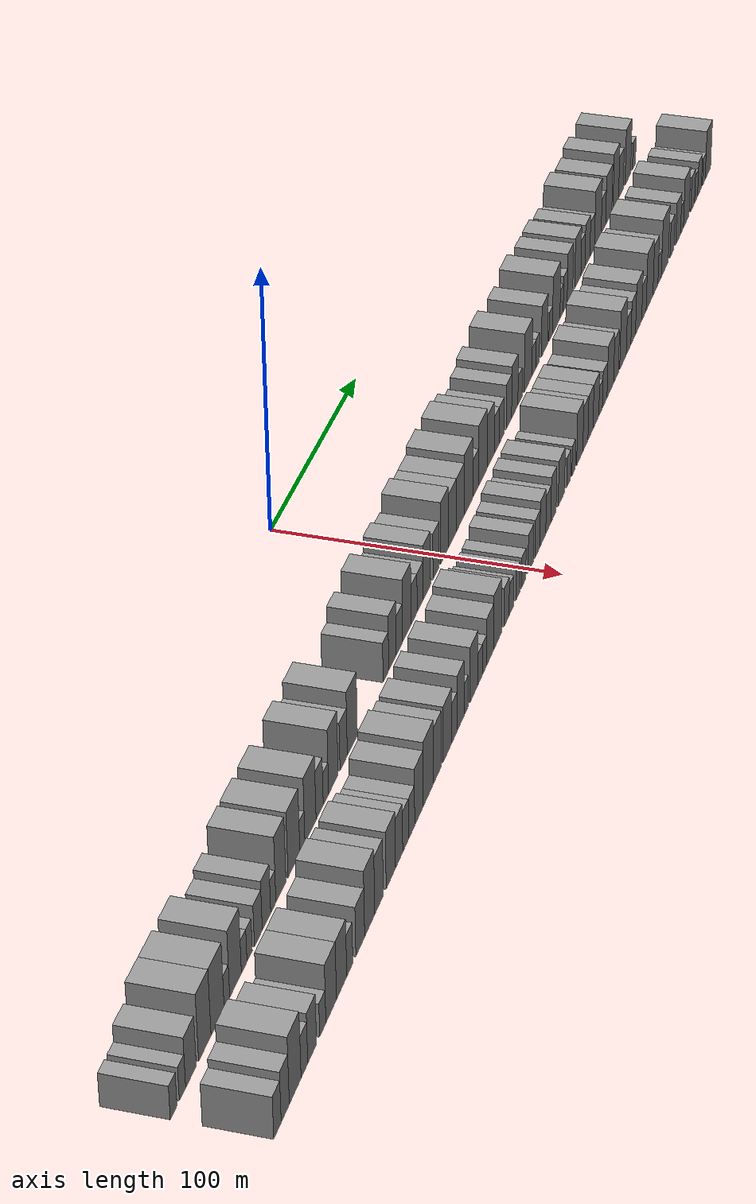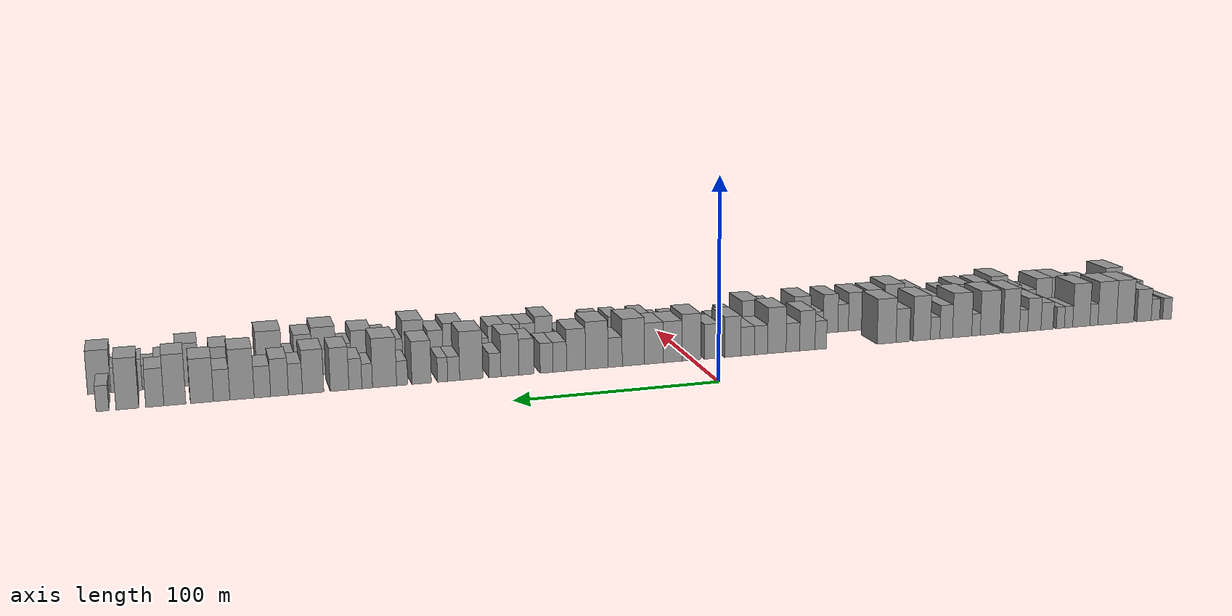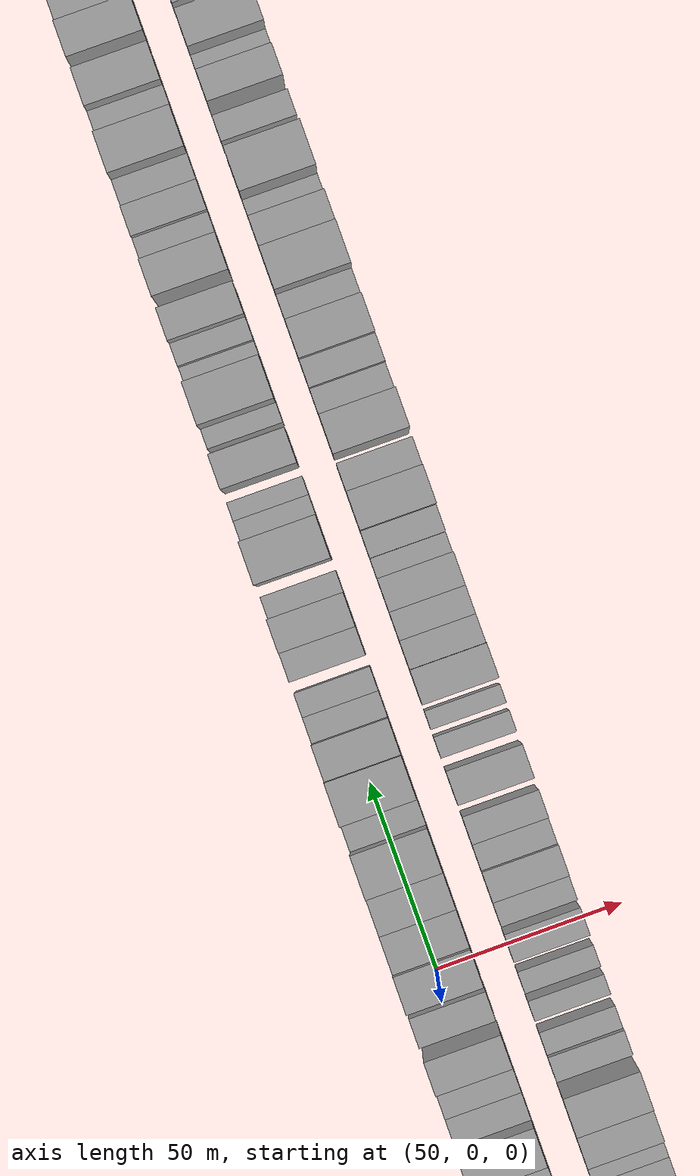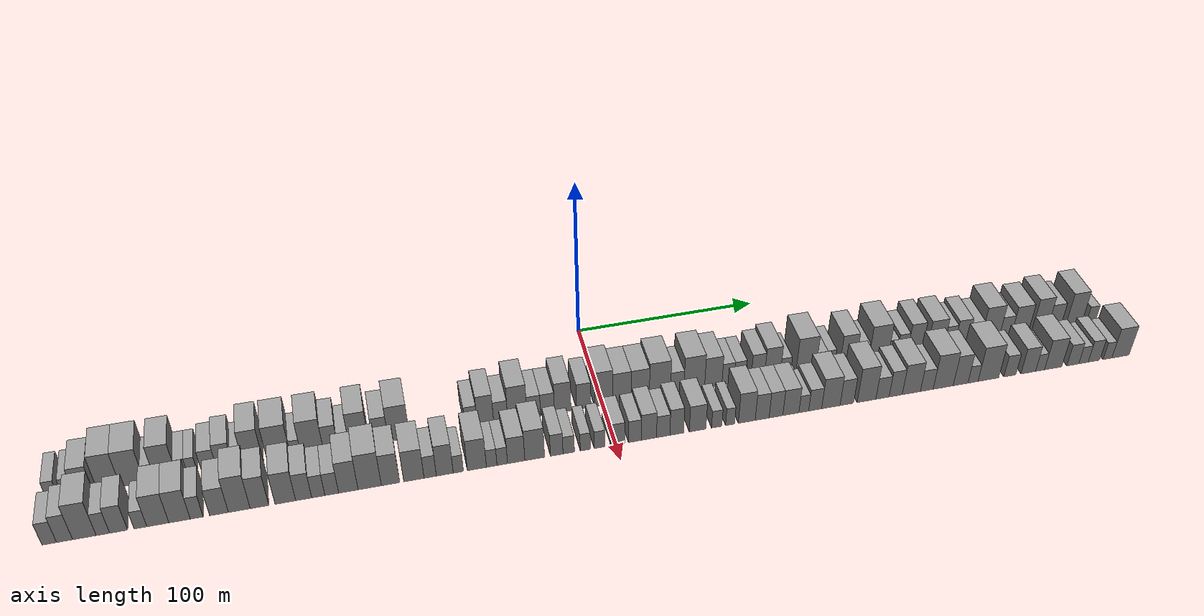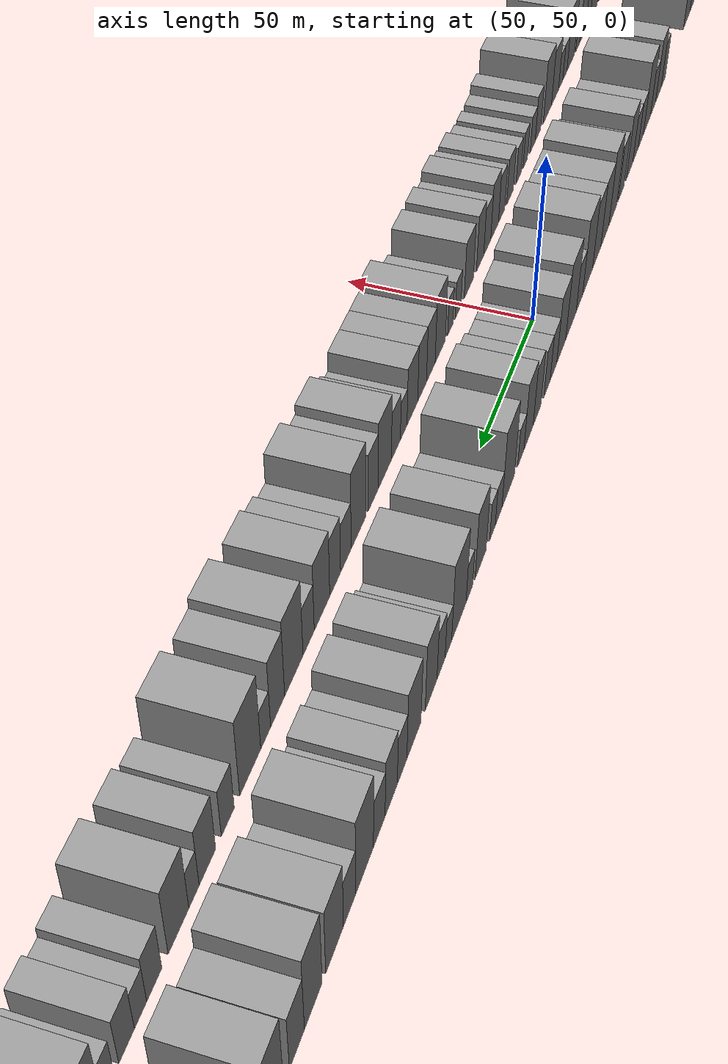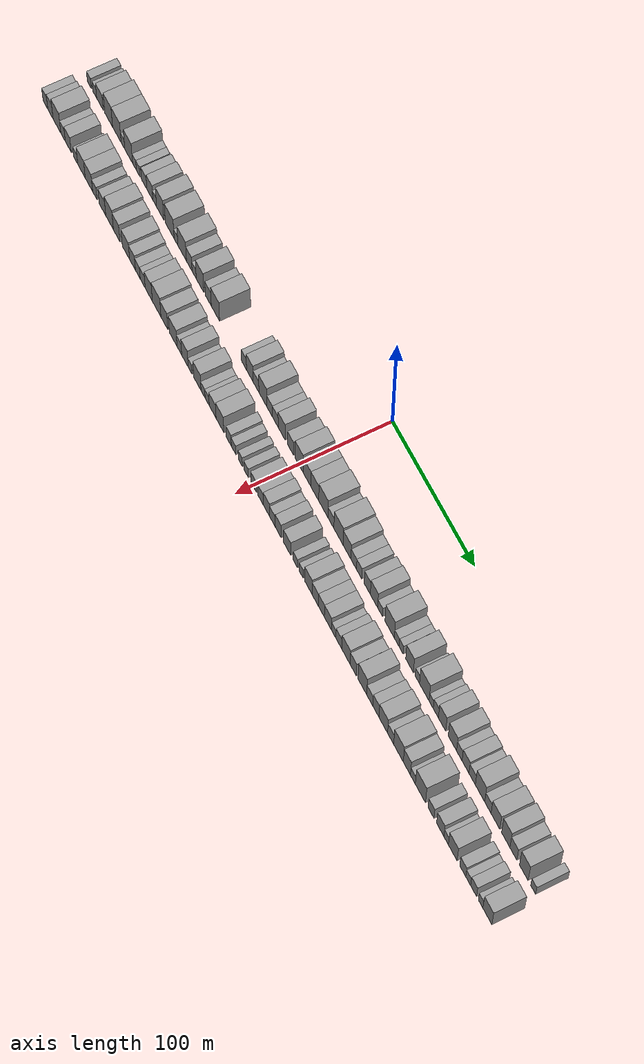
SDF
<sdf version="1.6">
 <world name="default">
  <scene>
   <sky><clouds><speed>12</speed></clouds></sky>
   <ambient>0.4 0.4 0.4 1</ambient>
   <background>0.7 0.7 0.7 1</background>
   <shadows>1</shadows>
  </scene>
  <gravity>0 0 -9.8066</gravity>
  <magnetic_field>6e-06 2.3e-05 -4.2e-05</magnetic_field>
  <physics default="0" name="default_physics" type="ode">
   <ode>
    <solver>
     <type>quick</type>
     <iters>10</iters>
     <sor>1.0</sor>
     <use_dynamic_moi_rescaling>0</use_dynamic_moi_rescaling>
    </solver>
    <constraints>
     <cfm>0</cfm>
     <erp>0.2</erp>
     <contact_max_correcting_vel>100</contact_max_correcting_vel>
     <contact_surface_layer>0.001</contact_surface_layer>
    </constraints>
   </ode>
   <max_step_size>0.004</max_step_size>
   <real_time_factor>1</real_time_factor>
   <real_time_update_rate>250</real_time_update_rate>
  </physics>
  <light name="sun" type="directional">
   <pose>0 0 10 0 0 0</pose>
   <diffuse>0.8 0.8 0.8 1</diffuse>
   <specular>0.2 0.2 0.2 1</specular>
   <attenuation>
    <range>1000</range>
    <constant>0.9</constant>
    <linear>0.01</linear>
    <quadratic>0.001</quadratic>
   </attenuation>
   <direction>-0.5 0.1 -0.9</direction>
  </light>
  <model name="building_1">
   <static>1</static>
   <pose>50.0000 -275.2254 0 0.000000 0.000000 0.000000</pose>
   <link name="link">
    <pose>0 0 6.00 0 0 0</pose>
    <collision name="collision"><geometry><box><size>20.0000 5.5493 12.0000</size></box></geometry></collision>
    <visual name="visual">
     <cast_shadows>0</cast_shadows>
     <geometry><box><size>20.0000 5.5493 12.0000</size></box></geometry>
     <material>
      <script>
       <uri>model://grey_wall/materials/scripts</uri>
       <uri>model://grey_wall/materials/textures</uri>
       <name>vrc/grey_wall</name>
      </script>
     </material>
    </visual>
   </link>
  </model>
  <model name="building_2">
   <static>1</static>
   <pose>50.0000 -267.8029 0 0.000000 0.000000 0.000000</pose>
   <link name="link">
    <pose>0 0 6.00 0 0 0</pose>
    <collision name="collision"><geometry><box><size>20.0000 5.2957 12.0000</size></box></geometry></collision>
    <visual name="visual">
     <cast_shadows>0</cast_shadows>
     <geometry><box><size>20.0000 5.2957 12.0000</size></box></geometry>
     <material>
      <script>
       <uri>model://grey_wall/materials/scripts</uri>
       <uri>model://grey_wall/materials/textures</uri>
       <name>vrc/grey_wall</name>
      </script>
     </material>
    </visual>
   </link>
  </model>
  <model name="building_3">
   <static>1</static>
   <pose>50.0000 -260.6596 0 0.000000 0.000000 0.000000</pose>
   <link name="link">
    <pose>0 0 9.00 0 0 0</pose>
    <collision name="collision"><geometry><box><size>20.0000 8.9908 18.0000</size></box></geometry></collision>
    <visual name="visual">
     <cast_shadows>0</cast_shadows>
     <geometry><box><size>20.0000 8.9908 18.0000</size></box></geometry>
     <material>
      <script>
       <uri>model://grey_wall/materials/scripts</uri>
       <uri>model://grey_wall/materials/textures</uri>
       <name>vrc/grey_wall</name>
      </script>
     </material>
    </visual>
   </link>
  </model>
  <model name="building_4">
   <static>1</static>
   <pose>50.0000 -248.7745 0 0.000000 0.000000 0.000000</pose>
   <link name="link">
    <pose>0 0 12.00 0 0 0</pose>
    <collision name="collision"><geometry><box><size>20.0000 10.7793 24.0000</size></box></geometry></collision>
    <visual name="visual">
     <cast_shadows>0</cast_shadows>
     <geometry><box><size>20.0000 10.7793 24.0000</size></box></geometry>
     <material>
      <script>
       <uri>model://grey_wall/materials/scripts</uri>
       <uri>model://grey_wall/materials/textures</uri>
       <name>vrc/grey_wall</name>
      </script>
     </material>
    </visual>
   </link>
  </model>
  <model name="building_5">
   <static>1</static>
   <pose>50.0000 -237.6013 0 0.000000 0.000000 0.000000</pose>
   <link name="link">
    <pose>0 0 12.00 0 0 0</pose>
    <collision name="collision"><geometry><box><size>20.0000 11.5671 24.0000</size></box></geometry></collision>
    <visual name="visual">
     <cast_shadows>0</cast_shadows>
     <geometry><box><size>20.0000 11.5671 24.0000</size></box></geometry>
     <material>
      <script>
       <uri>model://grey_wall/materials/scripts</uri>
       <uri>model://grey_wall/materials/textures</uri>
       <name>vrc/grey_wall</name>
      </script>
     </material>
    </visual>
   </link>
  </model>
  <model name="building_6">
   <static>1</static>
   <pose>50.0000 -229.3475 0 0.000000 0.000000 0.000000</pose>
   <link name="link">
    <pose>0 0 6.00 0 0 0</pose>
    <collision name="collision"><geometry><box><size>20.0000 4.9405 12.0000</size></box></geometry></collision>
    <visual name="visual">
     <cast_shadows>0</cast_shadows>
     <geometry><box><size>20.0000 4.9405 12.0000</size></box></geometry>
     <material>
      <script>
       <uri>model://grey_wall/materials/scripts</uri>
       <uri>model://grey_wall/materials/textures</uri>
       <name>vrc/grey_wall</name>
      </script>
     </material>
    </visual>
   </link>
  </model>
  <model name="building_7">
   <static>1</static>
   <pose>50.0000 -221.5886 0 0.000000 0.000000 0.000000</pose>
   <link name="link">
    <pose>0 0 12.00 0 0 0</pose>
    <collision name="collision"><geometry><box><size>20.0000 10.5772 24.0000</size></box></geometry></collision>
    <visual name="visual">
     <cast_shadows>0</cast_shadows>
     <geometry><box><size>20.0000 10.5772 24.0000</size></box></geometry>
     <material>
      <script>
       <uri>model://grey_wall/materials/scripts</uri>
       <uri>model://grey_wall/materials/textures</uri>
       <name>vrc/grey_wall</name>
      </script>
     </material>
    </visual>
   </link>
  </model>
  <model name="building_8">
   <static>1</static>
   <pose>50.0000 -213.7445 0 0.000000 0.000000 0.000000</pose>
   <link name="link">
    <pose>0 0 6.00 0 0 0</pose>
    <collision name="collision"><geometry><box><size>20.0000 5.1109 12.0000</size></box></geometry></collision>
    <visual name="visual">
     <cast_shadows>0</cast_shadows>
     <geometry><box><size>20.0000 5.1109 12.0000</size></box></geometry>
     <material>
      <script>
       <uri>model://grey_wall/materials/scripts</uri>
       <uri>model://grey_wall/materials/textures</uri>
       <name>vrc/grey_wall</name>
      </script>
     </material>
    </visual>
   </link>
  </model>
  <model name="building_9">
   <static>1</static>
   <pose>50.0000 -208.7607 0 0.000000 0.000000 0.000000</pose>
   <link name="link">
    <pose>0 0 6.00 0 0 0</pose>
    <collision name="collision"><geometry><box><size>20.0000 4.8567 12.0000</size></box></geometry></collision>
    <visual name="visual">
     <cast_shadows>0</cast_shadows>
     <geometry><box><size>20.0000 4.8567 12.0000</size></box></geometry>
     <material>
      <script>
       <uri>model://grey_wall/materials/scripts</uri>
       <uri>model://grey_wall/materials/textures</uri>
       <name>vrc/grey_wall</name>
      </script>
     </material>
    </visual>
   </link>
  </model>
  <model name="building_10">
   <static>1</static>
   <pose>50.0000 -200.6562 0 0.000000 0.000000 0.000000</pose>
   <link name="link">
    <pose>0 0 7.50 0 0 0</pose>
    <collision name="collision"><geometry><box><size>20.0000 7.3524 15.0000</size></box></geometry></collision>
    <visual name="visual">
     <cast_shadows>0</cast_shadows>
     <geometry><box><size>20.0000 7.3524 15.0000</size></box></geometry>
     <material>
      <script>
       <uri>model://grey_wall/materials/scripts</uri>
       <uri>model://grey_wall/materials/textures</uri>
       <name>vrc/grey_wall</name>
      </script>
     </material>
    </visual>
   </link>
  </model>
  <model name="building_11">
   <static>1</static>
   <pose>50.0000 -192.9936 0 0.000000 0.000000 0.000000</pose>
   <link name="link">
    <pose>0 0 9.00 0 0 0</pose>
    <collision name="collision"><geometry><box><size>20.0000 7.9729 18.0000</size></box></geometry></collision>
    <visual name="visual">
     <cast_shadows>0</cast_shadows>
     <geometry><box><size>20.0000 7.9729 18.0000</size></box></geometry>
     <material>
      <script>
       <uri>model://grey_wall/materials/scripts</uri>
       <uri>model://grey_wall/materials/textures</uri>
       <name>vrc/grey_wall</name>
      </script>
     </material>
    </visual>
   </link>
  </model>
  <model name="building_12">
   <static>1</static>
   <pose>50.0000 -186.5411 0 0.000000 0.000000 0.000000</pose>
   <link name="link">
    <pose>0 0 6.00 0 0 0</pose>
    <collision name="collision"><geometry><box><size>20.0000 4.9321 12.0000</size></box></geometry></collision>
    <visual name="visual">
     <cast_shadows>0</cast_shadows>
     <geometry><box><size>20.0000 4.9321 12.0000</size></box></geometry>
     <material>
      <script>
       <uri>model://grey_wall/materials/scripts</uri>
       <uri>model://grey_wall/materials/textures</uri>
       <name>vrc/grey_wall</name>
      </script>
     </material>
    </visual>
   </link>
  </model>
  <model name="building_13">
   <static>1</static>
   <pose>50.0000 -179.2054 0 0.000000 0.000000 0.000000</pose>
   <link name="link">
    <pose>0 0 12.00 0 0 0</pose>
    <collision name="collision"><geometry><box><size>20.0000 9.7393 24.0000</size></box></geometry></collision>
    <visual name="visual">
     <cast_shadows>0</cast_shadows>
     <geometry><box><size>20.0000 9.7393 24.0000</size></box></geometry>
     <material>
      <script>
       <uri>model://grey_wall/materials/scripts</uri>
       <uri>model://grey_wall/materials/textures</uri>
       <name>vrc/grey_wall</name>
      </script>
     </material>
    </visual>
   </link>
  </model>
  <model name="building_14">
   <static>1</static>
   <pose>50.0000 -166.5232 0 0.000000 0.000000 0.000000</pose>
   <link name="link">
    <pose>0 0 12.00 0 0 0</pose>
    <collision name="collision"><geometry><box><size>20.0000 11.6252 24.0000</size></box></geometry></collision>
    <visual name="visual">
     <cast_shadows>0</cast_shadows>
     <geometry><box><size>20.0000 11.6252 24.0000</size></box></geometry>
     <material>
      <script>
       <uri>model://grey_wall/materials/scripts</uri>
       <uri>model://grey_wall/materials/textures</uri>
       <name>vrc/grey_wall</name>
      </script>
     </material>
    </visual>
   </link>
  </model>
  <model name="building_15">
   <static>1</static>
   <pose>50.0000 -158.1956 0 0.000000 0.000000 0.000000</pose>
   <link name="link">
    <pose>0 0 6.00 0 0 0</pose>
    <collision name="collision"><geometry><box><size>20.0000 5.0300 12.0000</size></box></geometry></collision>
    <visual name="visual">
     <cast_shadows>0</cast_shadows>
     <geometry><box><size>20.0000 5.0300 12.0000</size></box></geometry>
     <material>
      <script>
       <uri>model://grey_wall/materials/scripts</uri>
       <uri>model://grey_wall/materials/textures</uri>
       <name>vrc/grey_wall</name>
      </script>
     </material>
    </visual>
   </link>
  </model>
  <model name="building_16">
   <static>1</static>
   <pose>50.0000 -150.0507 0 0.000000 0.000000 0.000000</pose>
   <link name="link">
    <pose>0 0 12.00 0 0 0</pose>
    <collision name="collision"><geometry><box><size>20.0000 11.2597 24.0000</size></box></geometry></collision>
    <visual name="visual">
     <cast_shadows>0</cast_shadows>
     <geometry><box><size>20.0000 11.2597 24.0000</size></box></geometry>
     <material>
      <script>
       <uri>model://grey_wall/materials/scripts</uri>
       <uri>model://grey_wall/materials/textures</uri>
       <name>vrc/grey_wall</name>
      </script>
     </material>
    </visual>
   </link>
  </model>
  <model name="building_17">
   <static>1</static>
   <pose>50.0000 -140.7484 0 0.000000 0.000000 0.000000</pose>
   <link name="link">
    <pose>0 0 9.00 0 0 0</pose>
    <collision name="collision"><geometry><box><size>20.0000 7.3451 18.0000</size></box></geometry></collision>
    <visual name="visual">
     <cast_shadows>0</cast_shadows>
     <geometry><box><size>20.0000 7.3451 18.0000</size></box></geometry>
     <material>
      <script>
       <uri>model://grey_wall/materials/scripts</uri>
       <uri>model://grey_wall/materials/textures</uri>
       <name>vrc/grey_wall</name>
      </script>
     </material>
    </visual>
   </link>
  </model>
  <model name="building_18">
   <static>1</static>
   <pose>50.0000 -134.3213 0 0.000000 0.000000 0.000000</pose>
   <link name="link">
    <pose>0 0 6.00 0 0 0</pose>
    <collision name="collision"><geometry><box><size>20.0000 5.5092 12.0000</size></box></geometry></collision>
    <visual name="visual">
     <cast_shadows>0</cast_shadows>
     <geometry><box><size>20.0000 5.5092 12.0000</size></box></geometry>
     <material>
      <script>
       <uri>model://grey_wall/materials/scripts</uri>
       <uri>model://grey_wall/materials/textures</uri>
       <name>vrc/grey_wall</name>
      </script>
     </material>
    </visual>
   </link>
  </model>
  <model name="building_19">
   <static>1</static>
   <pose>50.0000 -126.6029 0 0.000000 0.000000 0.000000</pose>
   <link name="link">
    <pose>0 0 12.00 0 0 0</pose>
    <collision name="collision"><geometry><box><size>20.0000 9.9276 24.0000</size></box></geometry></collision>
    <visual name="visual">
     <cast_shadows>0</cast_shadows>
     <geometry><box><size>20.0000 9.9276 24.0000</size></box></geometry>
     <material>
      <script>
       <uri>model://grey_wall/materials/scripts</uri>
       <uri>model://grey_wall/materials/textures</uri>
       <name>vrc/grey_wall</name>
      </script>
     </material>
    </visual>
   </link>
  </model>
  <model name="building_20">
   <static>1</static>
   <pose>50.0000 -115.7636 0 0.000000 0.000000 0.000000</pose>
   <link name="link">
    <pose>0 0 9.00 0 0 0</pose>
    <collision name="collision"><geometry><box><size>20.0000 7.7510 18.0000</size></box></geometry></collision>
    <visual name="visual">
     <cast_shadows>0</cast_shadows>
     <geometry><box><size>20.0000 7.7510 18.0000</size></box></geometry>
     <material>
      <script>
       <uri>model://grey_wall/materials/scripts</uri>
       <uri>model://grey_wall/materials/textures</uri>
       <name>vrc/grey_wall</name>
      </script>
     </material>
    </visual>
   </link>
  </model>
  <model name="building_21">
   <static>1</static>
   <pose>50.0000 -106.4737 0 0.000000 0.000000 0.000000</pose>
   <link name="link">
    <pose>0 0 12.00 0 0 0</pose>
    <collision name="collision"><geometry><box><size>20.0000 10.8287 24.0000</size></box></geometry></collision>
    <visual name="visual">
     <cast_shadows>0</cast_shadows>
     <geometry><box><size>20.0000 10.8287 24.0000</size></box></geometry>
     <material>
      <script>
       <uri>model://grey_wall/materials/scripts</uri>
       <uri>model://grey_wall/materials/textures</uri>
       <name>vrc/grey_wall</name>
      </script>
     </material>
    </visual>
   </link>
  </model>
  <model name="building_22">
   <static>1</static>
   <pose>50.0000 -69.4700 0 0.000000 0.000000 0.000000</pose>
   <link name="link">
    <pose>0 0 7.50 0 0 0</pose>
    <collision name="collision"><geometry><box><size>20.0000 6.3929 15.0000</size></box></geometry></collision>
    <visual name="visual">
     <cast_shadows>0</cast_shadows>
     <geometry><box><size>20.0000 6.3929 15.0000</size></box></geometry>
     <material>
      <script>
       <uri>model://grey_wall/materials/scripts</uri>
       <uri>model://grey_wall/materials/textures</uri>
       <name>vrc/grey_wall</name>
      </script>
     </material>
    </visual>
   </link>
  </model>
  <model name="building_23">
   <static>1</static>
   <pose>50.0000 -62.0235 0 0.000000 0.000000 0.000000</pose>
   <link name="link">
    <pose>0 0 10.50 0 0 0</pose>
    <collision name="collision"><geometry><box><size>20.0000 8.5001 21.0000</size></box></geometry></collision>
    <visual name="visual">
     <cast_shadows>0</cast_shadows>
     <geometry><box><size>20.0000 8.5001 21.0000</size></box></geometry>
     <material>
      <script>
       <uri>model://grey_wall/materials/scripts</uri>
       <uri>model://grey_wall/materials/textures</uri>
       <name>vrc/grey_wall</name>
      </script>
     </material>
    </visual>
   </link>
  </model>
  <model name="building_24">
   <static>1</static>
   <pose>50.0000 -54.0751 0 0.000000 0.000000 0.000000</pose>
   <link name="link">
    <pose>0 0 7.50 0 0 0</pose>
    <collision name="collision"><geometry><box><size>20.0000 7.3966 15.0000</size></box></geometry></collision>
    <visual name="visual">
     <cast_shadows>0</cast_shadows>
     <geometry><box><size>20.0000 7.3966 15.0000</size></box></geometry>
     <material>
      <script>
       <uri>model://grey_wall/materials/scripts</uri>
       <uri>model://grey_wall/materials/textures</uri>
       <name>vrc/grey_wall</name>
      </script>
     </material>
    </visual>
   </link>
  </model>
  <model name="building_25">
   <static>1</static>
   <pose>50.0000 -45.3534 0 0.000000 0.000000 0.000000</pose>
   <link name="link">
    <pose>0 0 12.00 0 0 0</pose>
    <collision name="collision"><geometry><box><size>20.0000 10.0468 24.0000</size></box></geometry></collision>
    <visual name="visual">
     <cast_shadows>0</cast_shadows>
     <geometry><box><size>20.0000 10.0468 24.0000</size></box></geometry>
     <material>
      <script>
       <uri>model://grey_wall/materials/scripts</uri>
       <uri>model://grey_wall/materials/textures</uri>
       <name>vrc/grey_wall</name>
      </script>
     </material>
    </visual>
   </link>
  </model>
  <model name="building_26">
   <static>1</static>
   <pose>50.0000 -36.7470 0 0.000000 0.000000 0.000000</pose>
   <link name="link">
    <pose>0 0 7.50 0 0 0</pose>
    <collision name="collision"><geometry><box><size>20.0000 7.1660 15.0000</size></box></geometry></collision>
    <visual name="visual">
     <cast_shadows>0</cast_shadows>
     <geometry><box><size>20.0000 7.1660 15.0000</size></box></geometry>
     <material>
      <script>
       <uri>model://grey_wall/materials/scripts</uri>
       <uri>model://grey_wall/materials/textures</uri>
       <name>vrc/grey_wall</name>
      </script>
     </material>
    </visual>
   </link>
  </model>
  <model name="building_27">
   <static>1</static>
   <pose>50.0000 -29.4997 0 0.000000 0.000000 0.000000</pose>
   <link name="link">
    <pose>0 0 7.50 0 0 0</pose>
    <collision name="collision"><geometry><box><size>20.0000 7.3286 15.0000</size></box></geometry></collision>
    <visual name="visual">
     <cast_shadows>0</cast_shadows>
     <geometry><box><size>20.0000 7.3286 15.0000</size></box></geometry>
     <material>
      <script>
       <uri>model://grey_wall/materials/scripts</uri>
       <uri>model://grey_wall/materials/textures</uri>
       <name>vrc/grey_wall</name>
      </script>
     </material>
    </visual>
   </link>
  </model>
  <model name="building_28">
   <static>1</static>
   <pose>50.0000 -21.4595 0 0.000000 0.000000 0.000000</pose>
   <link name="link">
    <pose>0 0 10.50 0 0 0</pose>
    <collision name="collision"><geometry><box><size>20.0000 8.7516 21.0000</size></box></geometry></collision>
    <visual name="visual">
     <cast_shadows>0</cast_shadows>
     <geometry><box><size>20.0000 8.7516 21.0000</size></box></geometry>
     <material>
      <script>
       <uri>model://grey_wall/materials/scripts</uri>
       <uri>model://grey_wall/materials/textures</uri>
       <name>vrc/grey_wall</name>
      </script>
     </material>
    </visual>
   </link>
  </model>
  <model name="building_29">
   <static>1</static>
   <pose>50.0000 -10.2537 0 0.000000 0.000000 0.000000</pose>
   <link name="link">
    <pose>0 0 9.00 0 0 0</pose>
    <collision name="collision"><geometry><box><size>20.0000 7.6600 18.0000</size></box></geometry></collision>
    <visual name="visual">
     <cast_shadows>0</cast_shadows>
     <geometry><box><size>20.0000 7.6600 18.0000</size></box></geometry>
     <material>
      <script>
       <uri>model://grey_wall/materials/scripts</uri>
       <uri>model://grey_wall/materials/textures</uri>
       <name>vrc/grey_wall</name>
      </script>
     </material>
    </visual>
   </link>
  </model>
  <model name="building_30">
   <static>1</static>
   <pose>50.0000 0.4802 0 0.000000 0.000000 0.000000</pose>
   <link name="link">
    <pose>0 0 12.00 0 0 0</pose>
    <collision name="collision"><geometry><box><size>20.0000 9.8076 24.0000</size></box></geometry></collision>
    <visual name="visual">
     <cast_shadows>0</cast_shadows>
     <geometry><box><size>20.0000 9.8076 24.0000</size></box></geometry>
     <material>
      <script>
       <uri>model://grey_wall/materials/scripts</uri>
       <uri>model://grey_wall/materials/textures</uri>
       <name>vrc/grey_wall</name>
      </script>
     </material>
    </visual>
   </link>
  </model>
  <model name="building_31">
   <static>1</static>
   <pose>50.0000 10.3010 0 0.000000 0.000000 0.000000</pose>
   <link name="link">
    <pose>0 0 10.50 0 0 0</pose>
    <collision name="collision"><geometry><box><size>20.0000 9.8340 21.0000</size></box></geometry></collision>
    <visual name="visual">
     <cast_shadows>0</cast_shadows>
     <geometry><box><size>20.0000 9.8340 21.0000</size></box></geometry>
     <material>
      <script>
       <uri>model://grey_wall/materials/scripts</uri>
       <uri>model://grey_wall/materials/textures</uri>
       <name>vrc/grey_wall</name>
      </script>
     </material>
    </visual>
   </link>
  </model>
  <model name="building_32">
   <static>1</static>
   <pose>50.0000 20.1373 0 0.000000 0.000000 0.000000</pose>
   <link name="link">
    <pose>0 0 10.50 0 0 0</pose>
    <collision name="collision"><geometry><box><size>20.0000 9.8388 21.0000</size></box></geometry></collision>
    <visual name="visual">
     <cast_shadows>0</cast_shadows>
     <geometry><box><size>20.0000 9.8388 21.0000</size></box></geometry>
     <material>
      <script>
       <uri>model://grey_wall/materials/scripts</uri>
       <uri>model://grey_wall/materials/textures</uri>
       <name>vrc/grey_wall</name>
      </script>
     </material>
    </visual>
   </link>
  </model>
  <model name="building_33">
   <static>1</static>
   <pose>50.0000 30.8102 0 0.000000 0.000000 0.000000</pose>
   <link name="link">
    <pose>0 0 12.00 0 0 0</pose>
    <collision name="collision"><geometry><box><size>20.0000 11.5070 24.0000</size></box></geometry></collision>
    <visual name="visual">
     <cast_shadows>0</cast_shadows>
     <geometry><box><size>20.0000 11.5070 24.0000</size></box></geometry>
     <material>
      <script>
       <uri>model://grey_wall/materials/scripts</uri>
       <uri>model://grey_wall/materials/textures</uri>
       <name>vrc/grey_wall</name>
      </script>
     </material>
    </visual>
   </link>
  </model>
  <model name="building_34">
   <static>1</static>
   <pose>50.0000 40.2271 0 0.000000 0.000000 0.000000</pose>
   <link name="link">
    <pose>0 0 7.50 0 0 0</pose>
    <collision name="collision"><geometry><box><size>20.0000 7.3268 15.0000</size></box></geometry></collision>
    <visual name="visual">
     <cast_shadows>0</cast_shadows>
     <geometry><box><size>20.0000 7.3268 15.0000</size></box></geometry>
     <material>
      <script>
       <uri>model://grey_wall/materials/scripts</uri>
       <uri>model://grey_wall/materials/textures</uri>
       <name>vrc/grey_wall</name>
      </script>
     </material>
    </visual>
   </link>
  </model>
  <model name="building_35">
   <static>1</static>
   <pose>50.0000 49.6016 0 0.000000 0.000000 0.000000</pose>
   <link name="link">
    <pose>0 0 12.00 0 0 0</pose>
    <collision name="collision"><geometry><box><size>20.0000 11.4222 24.0000</size></box></geometry></collision>
    <visual name="visual">
     <cast_shadows>0</cast_shadows>
     <geometry><box><size>20.0000 11.4222 24.0000</size></box></geometry>
     <material>
      <script>
       <uri>model://grey_wall/materials/scripts</uri>
       <uri>model://grey_wall/materials/textures</uri>
       <name>vrc/grey_wall</name>
      </script>
     </material>
    </visual>
   </link>
  </model>
  <model name="building_36">
   <static>1</static>
   <pose>50.0000 60.0975 0 0.000000 0.000000 0.000000</pose>
   <link name="link">
    <pose>0 0 10.50 0 0 0</pose>
    <collision name="collision"><geometry><box><size>20.0000 9.5696 21.0000</size></box></geometry></collision>
    <visual name="visual">
     <cast_shadows>0</cast_shadows>
     <geometry><box><size>20.0000 9.5696 21.0000</size></box></geometry>
     <material>
      <script>
       <uri>model://grey_wall/materials/scripts</uri>
       <uri>model://grey_wall/materials/textures</uri>
       <name>vrc/grey_wall</name>
      </script>
     </material>
    </visual>
   </link>
  </model>
  <model name="building_37">
   <static>1</static>
   <pose>50.0000 68.3081 0 0.000000 0.000000 0.000000</pose>
   <link name="link">
    <pose>0 0 7.50 0 0 0</pose>
    <collision name="collision"><geometry><box><size>20.0000 6.8517 15.0000</size></box></geometry></collision>
    <visual name="visual">
     <cast_shadows>0</cast_shadows>
     <geometry><box><size>20.0000 6.8517 15.0000</size></box></geometry>
     <material>
      <script>
       <uri>model://grey_wall/materials/scripts</uri>
       <uri>model://grey_wall/materials/textures</uri>
       <name>vrc/grey_wall</name>
      </script>
     </material>
    </visual>
   </link>
  </model>
  <model name="building_38">
   <static>1</static>
   <pose>50.0000 74.9236 0 0.000000 0.000000 0.000000</pose>
   <link name="link">
    <pose>0 0 7.50 0 0 0</pose>
    <collision name="collision"><geometry><box><size>20.0000 6.3793 15.0000</size></box></geometry></collision>
    <visual name="visual">
     <cast_shadows>0</cast_shadows>
     <geometry><box><size>20.0000 6.3793 15.0000</size></box></geometry>
     <material>
      <script>
       <uri>model://grey_wall/materials/scripts</uri>
       <uri>model://grey_wall/materials/textures</uri>
       <name>vrc/grey_wall</name>
      </script>
     </material>
    </visual>
   </link>
  </model>
  <model name="building_39">
   <static>1</static>
   <pose>50.0000 84.8796 0 0.000000 0.000000 0.000000</pose>
   <link name="link">
    <pose>0 0 9.00 0 0 0</pose>
    <collision name="collision"><geometry><box><size>20.0000 7.5326 18.0000</size></box></geometry></collision>
    <visual name="visual">
     <cast_shadows>0</cast_shadows>
     <geometry><box><size>20.0000 7.5326 18.0000</size></box></geometry>
     <material>
      <script>
       <uri>model://grey_wall/materials/scripts</uri>
       <uri>model://grey_wall/materials/textures</uri>
       <name>vrc/grey_wall</name>
      </script>
     </material>
    </visual>
   </link>
  </model>
  <model name="building_40">
   <static>1</static>
   <pose>50.0000 93.0982 0 0.000000 0.000000 0.000000</pose>
   <link name="link">
    <pose>0 0 10.50 0 0 0</pose>
    <collision name="collision"><geometry><box><size>20.0000 8.9047 21.0000</size></box></geometry></collision>
    <visual name="visual">
     <cast_shadows>0</cast_shadows>
     <geometry><box><size>20.0000 8.9047 21.0000</size></box></geometry>
     <material>
      <script>
       <uri>model://grey_wall/materials/scripts</uri>
       <uri>model://grey_wall/materials/textures</uri>
       <name>vrc/grey_wall</name>
      </script>
     </material>
    </visual>
   </link>
  </model>
  <model name="building_41">
   <static>1</static>
   <pose>50.0000 100.4825 0 0.000000 0.000000 0.000000</pose>
   <link name="link">
    <pose>0 0 6.00 0 0 0</pose>
    <collision name="collision"><geometry><box><size>20.0000 5.8639 12.0000</size></box></geometry></collision>
    <visual name="visual">
     <cast_shadows>0</cast_shadows>
     <geometry><box><size>20.0000 5.8639 12.0000</size></box></geometry>
     <material>
      <script>
       <uri>model://grey_wall/materials/scripts</uri>
       <uri>model://grey_wall/materials/textures</uri>
       <name>vrc/grey_wall</name>
      </script>
     </material>
    </visual>
   </link>
  </model>
  <model name="building_42">
   <static>1</static>
   <pose>50.0000 112.0596 0 0.000000 0.000000 0.000000</pose>
   <link name="link">
    <pose>0 0 12.00 0 0 0</pose>
    <collision name="collision"><geometry><box><size>20.0000 11.2903 24.0000</size></box></geometry></collision>
    <visual name="visual">
     <cast_shadows>0</cast_shadows>
     <geometry><box><size>20.0000 11.2903 24.0000</size></box></geometry>
     <material>
      <script>
       <uri>model://grey_wall/materials/scripts</uri>
       <uri>model://grey_wall/materials/textures</uri>
       <name>vrc/grey_wall</name>
      </script>
     </material>
    </visual>
   </link>
  </model>
  <model name="building_43">
   <static>1</static>
   <pose>50.0000 120.6020 0 0.000000 0.000000 0.000000</pose>
   <link name="link">
    <pose>0 0 6.00 0 0 0</pose>
    <collision name="collision"><geometry><box><size>20.0000 5.7946 12.0000</size></box></geometry></collision>
    <visual name="visual">
     <cast_shadows>0</cast_shadows>
     <geometry><box><size>20.0000 5.7946 12.0000</size></box></geometry>
     <material>
      <script>
       <uri>model://grey_wall/materials/scripts</uri>
       <uri>model://grey_wall/materials/textures</uri>
       <name>vrc/grey_wall</name>
      </script>
     </material>
    </visual>
   </link>
  </model>
  <model name="building_44">
   <static>1</static>
   <pose>50.0000 125.9452 0 0.000000 0.000000 0.000000</pose>
   <link name="link">
    <pose>0 0 6.00 0 0 0</pose>
    <collision name="collision"><geometry><box><size>20.0000 4.8918 12.0000</size></box></geometry></collision>
    <visual name="visual">
     <cast_shadows>0</cast_shadows>
     <geometry><box><size>20.0000 4.8918 12.0000</size></box></geometry>
     <material>
      <script>
       <uri>model://grey_wall/materials/scripts</uri>
       <uri>model://grey_wall/materials/textures</uri>
       <name>vrc/grey_wall</name>
      </script>
     </material>
    </visual>
   </link>
  </model>
  <model name="building_45">
   <static>1</static>
   <pose>50.0000 136.0157 0 0.000000 0.000000 0.000000</pose>
   <link name="link">
    <pose>0 0 10.50 0 0 0</pose>
    <collision name="collision"><geometry><box><size>20.0000 9.2492 21.0000</size></box></geometry></collision>
    <visual name="visual">
     <cast_shadows>0</cast_shadows>
     <geometry><box><size>20.0000 9.2492 21.0000</size></box></geometry>
     <material>
      <script>
       <uri>model://grey_wall/materials/scripts</uri>
       <uri>model://grey_wall/materials/textures</uri>
       <name>vrc/grey_wall</name>
      </script>
     </material>
    </visual>
   </link>
  </model>
  <model name="building_46">
   <static>1</static>
   <pose>50.0000 145.2747 0 0.000000 0.000000 0.000000</pose>
   <link name="link">
    <pose>0 0 6.00 0 0 0</pose>
    <collision name="collision"><geometry><box><size>20.0000 5.2688 12.0000</size></box></geometry></collision>
    <visual name="visual">
     <cast_shadows>0</cast_shadows>
     <geometry><box><size>20.0000 5.2688 12.0000</size></box></geometry>
     <material>
      <script>
       <uri>model://grey_wall/materials/scripts</uri>
       <uri>model://grey_wall/materials/textures</uri>
       <name>vrc/grey_wall</name>
      </script>
     </material>
    </visual>
   </link>
  </model>
  <model name="building_47">
   <static>1</static>
   <pose>50.0000 153.6020 0 0.000000 0.000000 0.000000</pose>
   <link name="link">
    <pose>0 0 12.00 0 0 0</pose>
    <collision name="collision"><geometry><box><size>20.0000 11.3859 24.0000</size></box></geometry></collision>
    <visual name="visual">
     <cast_shadows>0</cast_shadows>
     <geometry><box><size>20.0000 11.3859 24.0000</size></box></geometry>
     <material>
      <script>
       <uri>model://grey_wall/materials/scripts</uri>
       <uri>model://grey_wall/materials/textures</uri>
       <name>vrc/grey_wall</name>
      </script>
     </material>
    </visual>
   </link>
  </model>
  <model name="building_48">
   <static>1</static>
   <pose>50.0000 161.7843 0 0.000000 0.000000 0.000000</pose>
   <link name="link">
    <pose>0 0 6.00 0 0 0</pose>
    <collision name="collision"><geometry><box><size>20.0000 4.9787 12.0000</size></box></geometry></collision>
    <visual name="visual">
     <cast_shadows>0</cast_shadows>
     <geometry><box><size>20.0000 4.9787 12.0000</size></box></geometry>
     <material>
      <script>
       <uri>model://grey_wall/materials/scripts</uri>
       <uri>model://grey_wall/materials/textures</uri>
       <name>vrc/grey_wall</name>
      </script>
     </material>
    </visual>
   </link>
  </model>
  <model name="building_49">
   <static>1</static>
   <pose>50.0000 167.3069 0 0.000000 0.000000 0.000000</pose>
   <link name="link">
    <pose>0 0 7.50 0 0 0</pose>
    <collision name="collision"><geometry><box><size>20.0000 6.0666 15.0000</size></box></geometry></collision>
    <visual name="visual">
     <cast_shadows>0</cast_shadows>
     <geometry><box><size>20.0000 6.0666 15.0000</size></box></geometry>
     <material>
      <script>
       <uri>model://grey_wall/materials/scripts</uri>
       <uri>model://grey_wall/materials/textures</uri>
       <name>vrc/grey_wall</name>
      </script>
     </material>
    </visual>
   </link>
  </model>
  <model name="building_50">
   <static>1</static>
   <pose>50.0000 174.6600 0 0.000000 0.000000 0.000000</pose>
   <link name="link">
    <pose>0 0 10.50 0 0 0</pose>
    <collision name="collision"><geometry><box><size>20.0000 8.6395 21.0000</size></box></geometry></collision>
    <visual name="visual">
     <cast_shadows>0</cast_shadows>
     <geometry><box><size>20.0000 8.6395 21.0000</size></box></geometry>
     <material>
      <script>
       <uri>model://grey_wall/materials/scripts</uri>
       <uri>model://grey_wall/materials/textures</uri>
       <name>vrc/grey_wall</name>
      </script>
     </material>
    </visual>
   </link>
  </model>
  <model name="building_51">
   <static>1</static>
   <pose>50.0000 186.8944 0 0.000000 0.000000 0.000000</pose>
   <link name="link">
    <pose>0 0 10.50 0 0 0</pose>
    <collision name="collision"><geometry><box><size>20.0000 9.8294 21.0000</size></box></geometry></collision>
    <visual name="visual">
     <cast_shadows>0</cast_shadows>
     <geometry><box><size>20.0000 9.8294 21.0000</size></box></geometry>
     <material>
      <script>
       <uri>model://grey_wall/materials/scripts</uri>
       <uri>model://grey_wall/materials/textures</uri>
       <name>vrc/grey_wall</name>
      </script>
     </material>
    </visual>
   </link>
  </model>
  <model name="building_52">
   <static>1</static>
   <pose>50.0000 195.0261 0 0.000000 0.000000 0.000000</pose>
   <link name="link">
    <pose>0 0 7.50 0 0 0</pose>
    <collision name="collision"><geometry><box><size>20.0000 6.4340 15.0000</size></box></geometry></collision>
    <visual name="visual">
     <cast_shadows>0</cast_shadows>
     <geometry><box><size>20.0000 6.4340 15.0000</size></box></geometry>
     <material>
      <script>
       <uri>model://grey_wall/materials/scripts</uri>
       <uri>model://grey_wall/materials/textures</uri>
       <name>vrc/grey_wall</name>
      </script>
     </material>
    </visual>
   </link>
  </model>
  <model name="building_53">
   <static>1</static>
   <pose>50.0000 202.2781 0 0.000000 0.000000 0.000000</pose>
   <link name="link">
    <pose>0 0 9.00 0 0 0</pose>
    <collision name="collision"><geometry><box><size>20.0000 8.0700 18.0000</size></box></geometry></collision>
    <visual name="visual">
     <cast_shadows>0</cast_shadows>
     <geometry><box><size>20.0000 8.0700 18.0000</size></box></geometry>
     <material>
      <script>
       <uri>model://grey_wall/materials/scripts</uri>
       <uri>model://grey_wall/materials/textures</uri>
       <name>vrc/grey_wall</name>
      </script>
     </material>
    </visual>
   </link>
  </model>
  <model name="building_54">
   <static>1</static>
   <pose>50.0000 210.0287 0 0.000000 0.000000 0.000000</pose>
   <link name="link">
    <pose>0 0 7.50 0 0 0</pose>
    <collision name="collision"><geometry><box><size>20.0000 7.4312 15.0000</size></box></geometry></collision>
    <visual name="visual">
     <cast_shadows>0</cast_shadows>
     <geometry><box><size>20.0000 7.4312 15.0000</size></box></geometry>
     <material>
      <script>
       <uri>model://grey_wall/materials/scripts</uri>
       <uri>model://grey_wall/materials/textures</uri>
       <name>vrc/grey_wall</name>
      </script>
     </material>
    </visual>
   </link>
  </model>
  <model name="building_55">
   <static>1</static>
   <pose>50.0000 219.2063 0 0.000000 0.000000 0.000000</pose>
   <link name="link">
    <pose>0 0 12.00 0 0 0</pose>
    <collision name="collision"><geometry><box><size>20.0000 10.9239 24.0000</size></box></geometry></collision>
    <visual name="visual">
     <cast_shadows>0</cast_shadows>
     <geometry><box><size>20.0000 10.9239 24.0000</size></box></geometry>
     <material>
      <script>
       <uri>model://grey_wall/materials/scripts</uri>
       <uri>model://grey_wall/materials/textures</uri>
       <name>vrc/grey_wall</name>
      </script>
     </material>
    </visual>
   </link>
  </model>
  <model name="building_56">
   <static>1</static>
   <pose>50.0000 228.3347 0 0.000000 0.000000 0.000000</pose>
   <link name="link">
    <pose>0 0 7.50 0 0 0</pose>
    <collision name="collision"><geometry><box><size>20.0000 7.3330 15.0000</size></box></geometry></collision>
    <visual name="visual">
     <cast_shadows>0</cast_shadows>
     <geometry><box><size>20.0000 7.3330 15.0000</size></box></geometry>
     <material>
      <script>
       <uri>model://grey_wall/materials/scripts</uri>
       <uri>model://grey_wall/materials/textures</uri>
       <name>vrc/grey_wall</name>
      </script>
     </material>
    </visual>
   </link>
  </model>
  <model name="building_57">
   <static>1</static>
   <pose>50.0000 237.0896 0 0.000000 0.000000 0.000000</pose>
   <link name="link">
    <pose>0 0 10.50 0 0 0</pose>
    <collision name="collision"><geometry><box><size>20.0000 10.1768 21.0000</size></box></geometry></collision>
    <visual name="visual">
     <cast_shadows>0</cast_shadows>
     <geometry><box><size>20.0000 10.1768 21.0000</size></box></geometry>
     <material>
      <script>
       <uri>model://grey_wall/materials/scripts</uri>
       <uri>model://grey_wall/materials/textures</uri>
       <name>vrc/grey_wall</name>
      </script>
     </material>
    </visual>
   </link>
  </model>
  <model name="building_58">
   <static>1</static>
   <pose>50.0000 248.9940 0 0.000000 0.000000 0.000000</pose>
   <link name="link">
    <pose>0 0 12.00 0 0 0</pose>
    <collision name="collision"><geometry><box><size>20.0000 9.6319 24.0000</size></box></geometry></collision>
    <visual name="visual">
     <cast_shadows>0</cast_shadows>
     <geometry><box><size>20.0000 9.6319 24.0000</size></box></geometry>
     <material>
      <script>
       <uri>model://grey_wall/materials/scripts</uri>
       <uri>model://grey_wall/materials/textures</uri>
       <name>vrc/grey_wall</name>
      </script>
     </material>
    </visual>
   </link>
  </model>
  <model name="building_59">
   <static>1</static>
   <pose>50.0000 257.7727 0 0.000000 0.000000 0.000000</pose>
   <link name="link">
    <pose>0 0 9.00 0 0 0</pose>
    <collision name="collision"><geometry><box><size>20.0000 7.9254 18.0000</size></box></geometry></collision>
    <visual name="visual">
     <cast_shadows>0</cast_shadows>
     <geometry><box><size>20.0000 7.9254 18.0000</size></box></geometry>
     <material>
      <script>
       <uri>model://grey_wall/materials/scripts</uri>
       <uri>model://grey_wall/materials/textures</uri>
       <name>vrc/grey_wall</name>
      </script>
     </material>
    </visual>
   </link>
  </model>
  <model name="building_60">
   <static>1</static>
   <pose>50.0000 269.6629 0 0.000000 0.000000 0.000000</pose>
   <link name="link">
    <pose>0 0 12.00 0 0 0</pose>
    <collision name="collision"><geometry><box><size>20.0000 9.8551 24.0000</size></box></geometry></collision>
    <visual name="visual">
     <cast_shadows>0</cast_shadows>
     <geometry><box><size>20.0000 9.8551 24.0000</size></box></geometry>
     <material>
      <script>
       <uri>model://grey_wall/materials/scripts</uri>
       <uri>model://grey_wall/materials/textures</uri>
       <name>vrc/grey_wall</name>
      </script>
     </material>
    </visual>
   </link>
  </model>
  <model name="building_61">
   <static>1</static>
   <pose>50.0000 280.3805 0 0.000000 0.000000 0.000000</pose>
   <link name="link">
    <pose>0 0 6.00 0 0 0</pose>
    <collision name="collision"><geometry><box><size>20.0000 5.5799 12.0000</size></box></geometry></collision>
    <visual name="visual">
     <cast_shadows>0</cast_shadows>
     <geometry><box><size>20.0000 5.5799 12.0000</size></box></geometry>
     <material>
      <script>
       <uri>model://grey_wall/materials/scripts</uri>
       <uri>model://grey_wall/materials/textures</uri>
       <name>vrc/grey_wall</name>
      </script>
     </material>
    </visual>
   </link>
  </model>
  <model name="building_62">
   <static>1</static>
   <pose>79.0000 -274.7038 0 0.000000 0.000000 0.000000</pose>
   <link name="link">
    <pose>0 0 7.50 0 0 0</pose>
    <collision name="collision"><geometry><box><size>20.0000 6.5923 15.0000</size></box></geometry></collision>
    <visual name="visual">
     <cast_shadows>0</cast_shadows>
     <geometry><box><size>20.0000 6.5923 15.0000</size></box></geometry>
     <material>
      <script>
       <uri>model://grey_wall/materials/scripts</uri>
       <uri>model://grey_wall/materials/textures</uri>
       <name>vrc/grey_wall</name>
      </script>
     </material>
    </visual>
   </link>
  </model>
  <model name="building_63">
   <static>1</static>
   <pose>79.0000 -267.7580 0 0.000000 0.000000 0.000000</pose>
   <link name="link">
    <pose>0 0 9.00 0 0 0</pose>
    <collision name="collision"><geometry><box><size>20.0000 7.2993 18.0000</size></box></geometry></collision>
    <visual name="visual">
     <cast_shadows>0</cast_shadows>
     <geometry><box><size>20.0000 7.2993 18.0000</size></box></geometry>
     <material>
      <script>
       <uri>model://grey_wall/materials/scripts</uri>
       <uri>model://grey_wall/materials/textures</uri>
       <name>vrc/grey_wall</name>
      </script>
     </material>
    </visual>
   </link>
  </model>
  <model name="building_64">
   <static>1</static>
   <pose>79.0000 -258.7711 0 0.000000 0.000000 0.000000</pose>
   <link name="link">
    <pose>0 0 12.00 0 0 0</pose>
    <collision name="collision"><geometry><box><size>20.0000 10.6743 24.0000</size></box></geometry></collision>
    <visual name="visual">
     <cast_shadows>0</cast_shadows>
     <geometry><box><size>20.0000 10.6743 24.0000</size></box></geometry>
     <material>
      <script>
       <uri>model://grey_wall/materials/scripts</uri>
       <uri>model://grey_wall/materials/textures</uri>
       <name>vrc/grey_wall</name>
      </script>
     </material>
    </visual>
   </link>
  </model>
  <model name="building_65">
   <static>1</static>
   <pose>79.0000 -250.3494 0 0.000000 0.000000 0.000000</pose>
   <link name="link">
    <pose>0 0 7.50 0 0 0</pose>
    <collision name="collision"><geometry><box><size>20.0000 6.1691 15.0000</size></box></geometry></collision>
    <visual name="visual">
     <cast_shadows>0</cast_shadows>
     <geometry><box><size>20.0000 6.1691 15.0000</size></box></geometry>
     <material>
      <script>
       <uri>model://grey_wall/materials/scripts</uri>
       <uri>model://grey_wall/materials/textures</uri>
       <name>vrc/grey_wall</name>
      </script>
     </material>
    </visual>
   </link>
  </model>
  <model name="building_66">
   <static>1</static>
   <pose>79.0000 -243.1627 0 0.000000 0.000000 0.000000</pose>
   <link name="link">
    <pose>0 0 9.00 0 0 0</pose>
    <collision name="collision"><geometry><box><size>20.0000 8.2044 18.0000</size></box></geometry></collision>
    <visual name="visual">
     <cast_shadows>0</cast_shadows>
     <geometry><box><size>20.0000 8.2044 18.0000</size></box></geometry>
     <material>
      <script>
       <uri>model://grey_wall/materials/scripts</uri>
       <uri>model://grey_wall/materials/textures</uri>
       <name>vrc/grey_wall</name>
      </script>
     </material>
    </visual>
   </link>
  </model>
  <model name="building_67">
   <static>1</static>
   <pose>79.0000 -233.1358 0 0.000000 0.000000 0.000000</pose>
   <link name="link">
    <pose>0 0 6.00 0 0 0</pose>
    <collision name="collision"><geometry><box><size>20.0000 5.8494 12.0000</size></box></geometry></collision>
    <visual name="visual">
     <cast_shadows>0</cast_shadows>
     <geometry><box><size>20.0000 5.8494 12.0000</size></box></geometry>
     <material>
      <script>
       <uri>model://grey_wall/materials/scripts</uri>
       <uri>model://grey_wall/materials/textures</uri>
       <name>vrc/grey_wall</name>
      </script>
     </material>
    </visual>
   </link>
  </model>
  <model name="building_68">
   <static>1</static>
   <pose>79.0000 -225.1004 0 0.000000 0.000000 0.000000</pose>
   <link name="link">
    <pose>0 0 10.50 0 0 0</pose>
    <collision name="collision"><geometry><box><size>20.0000 10.2213 21.0000</size></box></geometry></collision>
    <visual name="visual">
     <cast_shadows>0</cast_shadows>
     <geometry><box><size>20.0000 10.2213 21.0000</size></box></geometry>
     <material>
      <script>
       <uri>model://grey_wall/materials/scripts</uri>
       <uri>model://grey_wall/materials/textures</uri>
       <name>vrc/grey_wall</name>
      </script>
     </material>
    </visual>
   </link>
  </model>
  <model name="building_69">
   <static>1</static>
   <pose>79.0000 -214.9961 0 0.000000 0.000000 0.000000</pose>
   <link name="link">
    <pose>0 0 10.50 0 0 0</pose>
    <collision name="collision"><geometry><box><size>20.0000 9.9872 21.0000</size></box></geometry></collision>
    <visual name="visual">
     <cast_shadows>0</cast_shadows>
     <geometry><box><size>20.0000 9.9872 21.0000</size></box></geometry>
     <material>
      <script>
       <uri>model://grey_wall/materials/scripts</uri>
       <uri>model://grey_wall/materials/textures</uri>
       <name>vrc/grey_wall</name>
      </script>
     </material>
    </visual>
   </link>
  </model>
  <model name="building_70">
   <static>1</static>
   <pose>79.0000 -206.9908 0 0.000000 0.000000 0.000000</pose>
   <link name="link">
    <pose>0 0 7.50 0 0 0</pose>
    <collision name="collision"><geometry><box><size>20.0000 6.0235 15.0000</size></box></geometry></collision>
    <visual name="visual">
     <cast_shadows>0</cast_shadows>
     <geometry><box><size>20.0000 6.0235 15.0000</size></box></geometry>
     <material>
      <script>
       <uri>model://grey_wall/materials/scripts</uri>
       <uri>model://grey_wall/materials/textures</uri>
       <name>vrc/grey_wall</name>
      </script>
     </material>
    </visual>
   </link>
  </model>
  <model name="building_71">
   <static>1</static>
   <pose>79.0000 -196.5531 0 0.000000 0.000000 0.000000</pose>
   <link name="link">
    <pose>0 0 9.00 0 0 0</pose>
    <collision name="collision"><geometry><box><size>20.0000 8.8519 18.0000</size></box></geometry></collision>
    <visual name="visual">
     <cast_shadows>0</cast_shadows>
     <geometry><box><size>20.0000 8.8519 18.0000</size></box></geometry>
     <material>
      <script>
       <uri>model://grey_wall/materials/scripts</uri>
       <uri>model://grey_wall/materials/textures</uri>
       <name>vrc/grey_wall</name>
      </script>
     </material>
    </visual>
   </link>
  </model>
  <model name="building_72">
   <static>1</static>
   <pose>79.0000 -186.9749 0 0.000000 0.000000 0.000000</pose>
   <link name="link">
    <pose>0 0 12.00 0 0 0</pose>
    <collision name="collision"><geometry><box><size>20.0000 10.3046 24.0000</size></box></geometry></collision>
    <visual name="visual">
     <cast_shadows>0</cast_shadows>
     <geometry><box><size>20.0000 10.3046 24.0000</size></box></geometry>
     <material>
      <script>
       <uri>model://grey_wall/materials/scripts</uri>
       <uri>model://grey_wall/materials/textures</uri>
       <name>vrc/grey_wall</name>
      </script>
     </material>
    </visual>
   </link>
  </model>
  <model name="building_73">
   <static>1</static>
   <pose>79.0000 -177.4079 0 0.000000 0.000000 0.000000</pose>
   <link name="link">
    <pose>0 0 10.50 0 0 0</pose>
    <collision name="collision"><geometry><box><size>20.0000 8.8294 21.0000</size></box></geometry></collision>
    <visual name="visual">
     <cast_shadows>0</cast_shadows>
     <geometry><box><size>20.0000 8.8294 21.0000</size></box></geometry>
     <material>
      <script>
       <uri>model://grey_wall/materials/scripts</uri>
       <uri>model://grey_wall/materials/textures</uri>
       <name>vrc/grey_wall</name>
      </script>
     </material>
    </visual>
   </link>
  </model>
  <model name="building_74">
   <static>1</static>
   <pose>79.0000 -165.0668 0 0.000000 0.000000 0.000000</pose>
   <link name="link">
    <pose>0 0 10.50 0 0 0</pose>
    <collision name="collision"><geometry><box><size>20.0000 9.8529 21.0000</size></box></geometry></collision>
    <visual name="visual">
     <cast_shadows>0</cast_shadows>
     <geometry><box><size>20.0000 9.8529 21.0000</size></box></geometry>
     <material>
      <script>
       <uri>model://grey_wall/materials/scripts</uri>
       <uri>model://grey_wall/materials/textures</uri>
       <name>vrc/grey_wall</name>
      </script>
     </material>
    </visual>
   </link>
  </model>
  <model name="building_75">
   <static>1</static>
   <pose>79.0000 -156.2728 0 0.000000 0.000000 0.000000</pose>
   <link name="link">
    <pose>0 0 9.00 0 0 0</pose>
    <collision name="collision"><geometry><box><size>20.0000 7.7352 18.0000</size></box></geometry></collision>
    <visual name="visual">
     <cast_shadows>0</cast_shadows>
     <geometry><box><size>20.0000 7.7352 18.0000</size></box></geometry>
     <material>
      <script>
       <uri>model://grey_wall/materials/scripts</uri>
       <uri>model://grey_wall/materials/textures</uri>
       <name>vrc/grey_wall</name>
      </script>
     </material>
    </visual>
   </link>
  </model>
  <model name="building_76">
   <static>1</static>
   <pose>79.0000 -149.2335 0 0.000000 0.000000 0.000000</pose>
   <link name="link">
    <pose>0 0 7.50 0 0 0</pose>
    <collision name="collision"><geometry><box><size>20.0000 6.3434 15.0000</size></box></geometry></collision>
    <visual name="visual">
     <cast_shadows>0</cast_shadows>
     <geometry><box><size>20.0000 6.3434 15.0000</size></box></geometry>
     <material>
      <script>
       <uri>model://grey_wall/materials/scripts</uri>
       <uri>model://grey_wall/materials/textures</uri>
       <name>vrc/grey_wall</name>
      </script>
     </material>
    </visual>
   </link>
  </model>
  <model name="building_77">
   <static>1</static>
   <pose>79.0000 -142.7230 0 0.000000 0.000000 0.000000</pose>
   <link name="link">
    <pose>0 0 7.50 0 0 0</pose>
    <collision name="collision"><geometry><box><size>20.0000 6.6776 15.0000</size></box></geometry></collision>
    <visual name="visual">
     <cast_shadows>0</cast_shadows>
     <geometry><box><size>20.0000 6.6776 15.0000</size></box></geometry>
     <material>
      <script>
       <uri>model://grey_wall/materials/scripts</uri>
       <uri>model://grey_wall/materials/textures</uri>
       <name>vrc/grey_wall</name>
      </script>
     </material>
    </visual>
   </link>
  </model>
  <model name="building_78">
   <static>1</static>
   <pose>79.0000 -134.6556 0 0.000000 0.000000 0.000000</pose>
   <link name="link">
    <pose>0 0 10.50 0 0 0</pose>
    <collision name="collision"><geometry><box><size>20.0000 9.4573 21.0000</size></box></geometry></collision>
    <visual name="visual">
     <cast_shadows>0</cast_shadows>
     <geometry><box><size>20.0000 9.4573 21.0000</size></box></geometry>
     <material>
      <script>
       <uri>model://grey_wall/materials/scripts</uri>
       <uri>model://grey_wall/materials/textures</uri>
       <name>vrc/grey_wall</name>
      </script>
     </material>
    </visual>
   </link>
  </model>
  <model name="building_79">
   <static>1</static>
   <pose>79.0000 -124.2389 0 0.000000 0.000000 0.000000</pose>
   <link name="link">
    <pose>0 0 12.00 0 0 0</pose>
    <collision name="collision"><geometry><box><size>20.0000 11.3761 24.0000</size></box></geometry></collision>
    <visual name="visual">
     <cast_shadows>0</cast_shadows>
     <geometry><box><size>20.0000 11.3761 24.0000</size></box></geometry>
     <material>
      <script>
       <uri>model://grey_wall/materials/scripts</uri>
       <uri>model://grey_wall/materials/textures</uri>
       <name>vrc/grey_wall</name>
      </script>
     </material>
    </visual>
   </link>
  </model>
  <model name="building_80">
   <static>1</static>
   <pose>79.0000 -114.0490 0 0.000000 0.000000 0.000000</pose>
   <link name="link">
    <pose>0 0 10.50 0 0 0</pose>
    <collision name="collision"><geometry><box><size>20.0000 9.0037 21.0000</size></box></geometry></collision>
    <visual name="visual">
     <cast_shadows>0</cast_shadows>
     <geometry><box><size>20.0000 9.0037 21.0000</size></box></geometry>
     <material>
      <script>
       <uri>model://grey_wall/materials/scripts</uri>
       <uri>model://grey_wall/materials/textures</uri>
       <name>vrc/grey_wall</name>
      </script>
     </material>
    </visual>
   </link>
  </model>
  <model name="building_81">
   <static>1</static>
   <pose>79.0000 -102.5260 0 0.000000 0.000000 0.000000</pose>
   <link name="link">
    <pose>0 0 10.50 0 0 0</pose>
    <collision name="collision"><geometry><box><size>20.0000 10.0424 21.0000</size></box></geometry></collision>
    <visual name="visual">
     <cast_shadows>0</cast_shadows>
     <geometry><box><size>20.0000 10.0424 21.0000</size></box></geometry>
     <material>
      <script>
       <uri>model://grey_wall/materials/scripts</uri>
       <uri>model://grey_wall/materials/textures</uri>
       <name>vrc/grey_wall</name>
      </script>
     </material>
    </visual>
   </link>
  </model>
  <model name="building_82">
   <static>1</static>
   <pose>79.0000 -94.4530 0 0.000000 0.000000 0.000000</pose>
   <link name="link">
    <pose>0 0 7.50 0 0 0</pose>
    <collision name="collision"><geometry><box><size>20.0000 6.1035 15.0000</size></box></geometry></collision>
    <visual name="visual">
     <cast_shadows>0</cast_shadows>
     <geometry><box><size>20.0000 6.1035 15.0000</size></box></geometry>
     <material>
      <script>
       <uri>model://grey_wall/materials/scripts</uri>
       <uri>model://grey_wall/materials/textures</uri>
       <name>vrc/grey_wall</name>
      </script>
     </material>
    </visual>
   </link>
  </model>
  <model name="building_83">
   <static>1</static>
   <pose>79.0000 -87.1955 0 0.000000 0.000000 0.000000</pose>
   <link name="link">
    <pose>0 0 10.50 0 0 0</pose>
    <collision name="collision"><geometry><box><size>20.0000 8.4114 21.0000</size></box></geometry></collision>
    <visual name="visual">
     <cast_shadows>0</cast_shadows>
     <geometry><box><size>20.0000 8.4114 21.0000</size></box></geometry>
     <material>
      <script>
       <uri>model://grey_wall/materials/scripts</uri>
       <uri>model://grey_wall/materials/textures</uri>
       <name>vrc/grey_wall</name>
      </script>
     </material>
    </visual>
   </link>
  </model>
  <model name="building_84">
   <static>1</static>
   <pose>79.0000 -80.4474 0 0.000000 0.000000 0.000000</pose>
   <link name="link">
    <pose>0 0 6.00 0 0 0</pose>
    <collision name="collision"><geometry><box><size>20.0000 5.0849 12.0000</size></box></geometry></collision>
    <visual name="visual">
     <cast_shadows>0</cast_shadows>
     <geometry><box><size>20.0000 5.0849 12.0000</size></box></geometry>
     <material>
      <script>
       <uri>model://grey_wall/materials/scripts</uri>
       <uri>model://grey_wall/materials/textures</uri>
       <name>vrc/grey_wall</name>
      </script>
     </material>
    </visual>
   </link>
  </model>
  <model name="building_85">
   <static>1</static>
   <pose>79.0000 -71.1343 0 0.000000 0.000000 0.000000</pose>
   <link name="link">
    <pose>0 0 10.50 0 0 0</pose>
    <collision name="collision"><geometry><box><size>20.0000 9.5413 21.0000</size></box></geometry></collision>
    <visual name="visual">
     <cast_shadows>0</cast_shadows>
     <geometry><box><size>20.0000 9.5413 21.0000</size></box></geometry>
     <material>
      <script>
       <uri>model://grey_wall/materials/scripts</uri>
       <uri>model://grey_wall/materials/textures</uri>
       <name>vrc/grey_wall</name>
      </script>
     </material>
    </visual>
   </link>
  </model>
  <model name="building_86">
   <static>1</static>
   <pose>79.0000 -63.6953 0 0.000000 0.000000 0.000000</pose>
   <link name="link">
    <pose>0 0 6.00 0 0 0</pose>
    <collision name="collision"><geometry><box><size>20.0000 5.3367 12.0000</size></box></geometry></collision>
    <visual name="visual">
     <cast_shadows>0</cast_shadows>
     <geometry><box><size>20.0000 5.3367 12.0000</size></box></geometry>
     <material>
      <script>
       <uri>model://grey_wall/materials/scripts</uri>
       <uri>model://grey_wall/materials/textures</uri>
       <name>vrc/grey_wall</name>
      </script>
     </material>
    </visual>
   </link>
  </model>
  <model name="building_87">
   <static>1</static>
   <pose>79.0000 -58.3521 0 0.000000 0.000000 0.000000</pose>
   <link name="link">
    <pose>0 0 6.00 0 0 0</pose>
    <collision name="collision"><geometry><box><size>20.0000 5.3498 12.0000</size></box></geometry></collision>
    <visual name="visual">
     <cast_shadows>0</cast_shadows>
     <geometry><box><size>20.0000 5.3498 12.0000</size></box></geometry>
     <material>
      <script>
       <uri>model://grey_wall/materials/scripts</uri>
       <uri>model://grey_wall/materials/textures</uri>
       <name>vrc/grey_wall</name>
      </script>
     </material>
    </visual>
   </link>
  </model>
  <model name="building_88">
   <static>1</static>
   <pose>79.0000 -51.2823 0 0.000000 0.000000 0.000000</pose>
   <link name="link">
    <pose>0 0 9.00 0 0 0</pose>
    <collision name="collision"><geometry><box><size>20.0000 8.7898 18.0000</size></box></geometry></collision>
    <visual name="visual">
     <cast_shadows>0</cast_shadows>
     <geometry><box><size>20.0000 8.7898 18.0000</size></box></geometry>
     <material>
      <script>
       <uri>model://grey_wall/materials/scripts</uri>
       <uri>model://grey_wall/materials/textures</uri>
       <name>vrc/grey_wall</name>
      </script>
     </material>
    </visual>
   </link>
  </model>
  <model name="building_89">
   <static>1</static>
   <pose>79.0000 -41.8593 0 0.000000 0.000000 0.000000</pose>
   <link name="link">
    <pose>0 0 10.50 0 0 0</pose>
    <collision name="collision"><geometry><box><size>20.0000 10.0562 21.0000</size></box></geometry></collision>
    <visual name="visual">
     <cast_shadows>0</cast_shadows>
     <geometry><box><size>20.0000 10.0562 21.0000</size></box></geometry>
     <material>
      <script>
       <uri>model://grey_wall/materials/scripts</uri>
       <uri>model://grey_wall/materials/textures</uri>
       <name>vrc/grey_wall</name>
      </script>
     </material>
    </visual>
   </link>
  </model>
  <model name="building_90">
   <static>1</static>
   <pose>79.0000 -30.5949 0 0.000000 0.000000 0.000000</pose>
   <link name="link">
    <pose>0 0 7.50 0 0 0</pose>
    <collision name="collision"><geometry><box><size>20.0000 6.4726 15.0000</size></box></geometry></collision>
    <visual name="visual">
     <cast_shadows>0</cast_shadows>
     <geometry><box><size>20.0000 6.4726 15.0000</size></box></geometry>
     <material>
      <script>
       <uri>model://grey_wall/materials/scripts</uri>
       <uri>model://grey_wall/materials/textures</uri>
       <name>vrc/grey_wall</name>
      </script>
     </material>
    </visual>
   </link>
  </model>
  <model name="building_91">
   <static>1</static>
   <pose>79.0000 -24.4163 0 0.000000 0.000000 0.000000</pose>
   <link name="link">
    <pose>0 0 6.00 0 0 0</pose>
    <collision name="collision"><geometry><box><size>20.0000 5.8846 12.0000</size></box></geometry></collision>
    <visual name="visual">
     <cast_shadows>0</cast_shadows>
     <geometry><box><size>20.0000 5.8846 12.0000</size></box></geometry>
     <material>
      <script>
       <uri>model://grey_wall/materials/scripts</uri>
       <uri>model://grey_wall/materials/textures</uri>
       <name>vrc/grey_wall</name>
      </script>
     </material>
    </visual>
   </link>
  </model>
  <model name="building_92">
   <static>1</static>
   <pose>79.0000 -15.8689 0 0.000000 0.000000 0.000000</pose>
   <link name="link">
    <pose>0 0 6.00 0 0 0</pose>
    <collision name="collision"><geometry><box><size>20.0000 5.2101 12.0000</size></box></geometry></collision>
    <visual name="visual">
     <cast_shadows>0</cast_shadows>
     <geometry><box><size>20.0000 5.2101 12.0000</size></box></geometry>
     <material>
      <script>
       <uri>model://grey_wall/materials/scripts</uri>
       <uri>model://grey_wall/materials/textures</uri>
       <name>vrc/grey_wall</name>
      </script>
     </material>
    </visual>
   </link>
  </model>
  <model name="building_93">
   <static>1</static>
   <pose>79.0000 -8.4298 0 0.000000 0.000000 0.000000</pose>
   <link name="link">
    <pose>0 0 6.00 0 0 0</pose>
    <collision name="collision"><geometry><box><size>20.0000 5.6682 12.0000</size></box></geometry></collision>
    <visual name="visual">
     <cast_shadows>0</cast_shadows>
     <geometry><box><size>20.0000 5.6682 12.0000</size></box></geometry>
     <material>
      <script>
       <uri>model://grey_wall/materials/scripts</uri>
       <uri>model://grey_wall/materials/textures</uri>
       <name>vrc/grey_wall</name>
      </script>
     </material>
    </visual>
   </link>
  </model>
  <model name="building_94">
   <static>1</static>
   <pose>79.0000 1.0166 0 0.000000 0.000000 0.000000</pose>
   <link name="link">
    <pose>0 0 7.50 0 0 0</pose>
    <collision name="collision"><geometry><box><size>20.0000 7.2247 15.0000</size></box></geometry></collision>
    <visual name="visual">
     <cast_shadows>0</cast_shadows>
     <geometry><box><size>20.0000 7.2247 15.0000</size></box></geometry>
     <material>
      <script>
       <uri>model://grey_wall/materials/scripts</uri>
       <uri>model://grey_wall/materials/textures</uri>
       <name>vrc/grey_wall</name>
      </script>
     </material>
    </visual>
   </link>
  </model>
  <model name="building_95">
   <static>1</static>
   <pose>79.0000 9.9615 0 0.000000 0.000000 0.000000</pose>
   <link name="link">
    <pose>0 0 7.50 0 0 0</pose>
    <collision name="collision"><geometry><box><size>20.0000 6.6652 15.0000</size></box></geometry></collision>
    <visual name="visual">
     <cast_shadows>0</cast_shadows>
     <geometry><box><size>20.0000 6.6652 15.0000</size></box></geometry>
     <material>
      <script>
       <uri>model://grey_wall/materials/scripts</uri>
       <uri>model://grey_wall/materials/textures</uri>
       <name>vrc/grey_wall</name>
      </script>
     </material>
    </visual>
   </link>
  </model>
  <model name="building_96">
   <static>1</static>
   <pose>79.0000 17.3039 0 0.000000 0.000000 0.000000</pose>
   <link name="link">
    <pose>0 0 9.00 0 0 0</pose>
    <collision name="collision"><geometry><box><size>20.0000 8.0195 18.0000</size></box></geometry></collision>
    <visual name="visual">
     <cast_shadows>0</cast_shadows>
     <geometry><box><size>20.0000 8.0195 18.0000</size></box></geometry>
     <material>
      <script>
       <uri>model://grey_wall/materials/scripts</uri>
       <uri>model://grey_wall/materials/textures</uri>
       <name>vrc/grey_wall</name>
      </script>
     </material>
    </visual>
   </link>
  </model>
  <model name="building_97">
   <static>1</static>
   <pose>79.0000 24.8488 0 0.000000 0.000000 0.000000</pose>
   <link name="link">
    <pose>0 0 7.50 0 0 0</pose>
    <collision name="collision"><geometry><box><size>20.0000 7.0703 15.0000</size></box></geometry></collision>
    <visual name="visual">
     <cast_shadows>0</cast_shadows>
     <geometry><box><size>20.0000 7.0703 15.0000</size></box></geometry>
     <material>
      <script>
       <uri>model://grey_wall/materials/scripts</uri>
       <uri>model://grey_wall/materials/textures</uri>
       <name>vrc/grey_wall</name>
      </script>
     </material>
    </visual>
   </link>
  </model>
  <model name="building_98">
   <static>1</static>
   <pose>79.0000 32.0305 0 0.000000 0.000000 0.000000</pose>
   <link name="link">
    <pose>0 0 9.00 0 0 0</pose>
    <collision name="collision"><geometry><box><size>20.0000 7.2931 18.0000</size></box></geometry></collision>
    <visual name="visual">
     <cast_shadows>0</cast_shadows>
     <geometry><box><size>20.0000 7.2931 18.0000</size></box></geometry>
     <material>
      <script>
       <uri>model://grey_wall/materials/scripts</uri>
       <uri>model://grey_wall/materials/textures</uri>
       <name>vrc/grey_wall</name>
      </script>
     </material>
    </visual>
   </link>
  </model>
  <model name="building_99">
   <static>1</static>
   <pose>79.0000 43.1184 0 0.000000 0.000000 0.000000</pose>
   <link name="link">
    <pose>0 0 9.00 0 0 0</pose>
    <collision name="collision"><geometry><box><size>20.0000 8.8828 18.0000</size></box></geometry></collision>
    <visual name="visual">
     <cast_shadows>0</cast_shadows>
     <geometry><box><size>20.0000 8.8828 18.0000</size></box></geometry>
     <material>
      <script>
       <uri>model://grey_wall/materials/scripts</uri>
       <uri>model://grey_wall/materials/textures</uri>
       <name>vrc/grey_wall</name>
      </script>
     </material>
    </visual>
   </link>
  </model>
  <model name="building_100">
   <static>1</static>
   <pose>79.0000 53.3364 0 0.000000 0.000000 0.000000</pose>
   <link name="link">
    <pose>0 0 6.00 0 0 0</pose>
    <collision name="collision"><geometry><box><size>20.0000 5.5532 12.0000</size></box></geometry></collision>
    <visual name="visual">
     <cast_shadows>0</cast_shadows>
     <geometry><box><size>20.0000 5.5532 12.0000</size></box></geometry>
     <material>
      <script>
       <uri>model://grey_wall/materials/scripts</uri>
       <uri>model://grey_wall/materials/textures</uri>
       <name>vrc/grey_wall</name>
      </script>
     </material>
    </visual>
   </link>
  </model>
  <model name="building_101">
   <static>1</static>
   <pose>79.0000 60.5450 0 0.000000 0.000000 0.000000</pose>
   <link name="link">
    <pose>0 0 6.00 0 0 0</pose>
    <collision name="collision"><geometry><box><size>20.0000 4.8638 12.0000</size></box></geometry></collision>
    <visual name="visual">
     <cast_shadows>0</cast_shadows>
     <geometry><box><size>20.0000 4.8638 12.0000</size></box></geometry>
     <material>
      <script>
       <uri>model://grey_wall/materials/scripts</uri>
       <uri>model://grey_wall/materials/textures</uri>
       <name>vrc/grey_wall</name>
      </script>
     </material>
    </visual>
   </link>
  </model>
  <model name="building_102">
   <static>1</static>
   <pose>79.0000 69.5289 0 0.000000 0.000000 0.000000</pose>
   <link name="link">
    <pose>0 0 10.50 0 0 0</pose>
    <collision name="collision"><geometry><box><size>20.0000 9.1040 21.0000</size></box></geometry></collision>
    <visual name="visual">
     <cast_shadows>0</cast_shadows>
     <geometry><box><size>20.0000 9.1040 21.0000</size></box></geometry>
     <material>
      <script>
       <uri>model://grey_wall/materials/scripts</uri>
       <uri>model://grey_wall/materials/textures</uri>
       <name>vrc/grey_wall</name>
      </script>
     </material>
    </visual>
   </link>
  </model>
  <model name="building_103">
   <static>1</static>
   <pose>79.0000 77.8512 0 0.000000 0.000000 0.000000</pose>
   <link name="link">
    <pose>0 0 9.00 0 0 0</pose>
    <collision name="collision"><geometry><box><size>20.0000 7.5407 18.0000</size></box></geometry></collision>
    <visual name="visual">
     <cast_shadows>0</cast_shadows>
     <geometry><box><size>20.0000 7.5407 18.0000</size></box></geometry>
     <material>
      <script>
       <uri>model://grey_wall/materials/scripts</uri>
       <uri>model://grey_wall/materials/textures</uri>
       <name>vrc/grey_wall</name>
      </script>
     </material>
    </visual>
   </link>
  </model>
  <model name="building_104">
   <static>1</static>
   <pose>79.0000 85.3609 0 0.000000 0.000000 0.000000</pose>
   <link name="link">
    <pose>0 0 9.00 0 0 0</pose>
    <collision name="collision"><geometry><box><size>20.0000 7.4787 18.0000</size></box></geometry></collision>
    <visual name="visual">
     <cast_shadows>0</cast_shadows>
     <geometry><box><size>20.0000 7.4787 18.0000</size></box></geometry>
     <material>
      <script>
       <uri>model://grey_wall/materials/scripts</uri>
       <uri>model://grey_wall/materials/textures</uri>
       <name>vrc/grey_wall</name>
      </script>
     </material>
    </visual>
   </link>
  </model>
  <model name="building_105">
   <static>1</static>
   <pose>79.0000 93.5083 0 0.000000 0.000000 0.000000</pose>
   <link name="link">
    <pose>0 0 9.00 0 0 0</pose>
    <collision name="collision"><geometry><box><size>20.0000 8.8161 18.0000</size></box></geometry></collision>
    <visual name="visual">
     <cast_shadows>0</cast_shadows>
     <geometry><box><size>20.0000 8.8161 18.0000</size></box></geometry>
     <material>
      <script>
       <uri>model://grey_wall/materials/scripts</uri>
       <uri>model://grey_wall/materials/textures</uri>
       <name>vrc/grey_wall</name>
      </script>
     </material>
    </visual>
   </link>
  </model>
  <model name="building_106">
   <static>1</static>
   <pose>79.0000 100.5982 0 0.000000 0.000000 0.000000</pose>
   <link name="link">
    <pose>0 0 6.00 0 0 0</pose>
    <collision name="collision"><geometry><box><size>20.0000 5.3637 12.0000</size></box></geometry></collision>
    <visual name="visual">
     <cast_shadows>0</cast_shadows>
     <geometry><box><size>20.0000 5.3637 12.0000</size></box></geometry>
     <material>
      <script>
       <uri>model://grey_wall/materials/scripts</uri>
       <uri>model://grey_wall/materials/textures</uri>
       <name>vrc/grey_wall</name>
      </script>
     </material>
    </visual>
   </link>
  </model>
  <model name="building_107">
   <static>1</static>
   <pose>79.0000 106.8569 0 0.000000 0.000000 0.000000</pose>
   <link name="link">
    <pose>0 0 7.50 0 0 0</pose>
    <collision name="collision"><geometry><box><size>20.0000 7.1536 15.0000</size></box></geometry></collision>
    <visual name="visual">
     <cast_shadows>0</cast_shadows>
     <geometry><box><size>20.0000 7.1536 15.0000</size></box></geometry>
     <material>
      <script>
       <uri>model://grey_wall/materials/scripts</uri>
       <uri>model://grey_wall/materials/textures</uri>
       <name>vrc/grey_wall</name>
      </script>
     </material>
    </visual>
   </link>
  </model>
  <model name="building_108">
   <static>1</static>
   <pose>79.0000 115.5226 0 0.000000 0.000000 0.000000</pose>
   <link name="link">
    <pose>0 0 10.50 0 0 0</pose>
    <collision name="collision"><geometry><box><size>20.0000 10.1778 21.0000</size></box></geometry></collision>
    <visual name="visual">
     <cast_shadows>0</cast_shadows>
     <geometry><box><size>20.0000 10.1778 21.0000</size></box></geometry>
     <material>
      <script>
       <uri>model://grey_wall/materials/scripts</uri>
       <uri>model://grey_wall/materials/textures</uri>
       <name>vrc/grey_wall</name>
      </script>
     </material>
    </visual>
   </link>
  </model>
  <model name="building_109">
   <static>1</static>
   <pose>79.0000 124.3724 0 0.000000 0.000000 0.000000</pose>
   <link name="link">
    <pose>0 0 9.00 0 0 0</pose>
    <collision name="collision"><geometry><box><size>20.0000 7.5217 18.0000</size></box></geometry></collision>
    <visual name="visual">
     <cast_shadows>0</cast_shadows>
     <geometry><box><size>20.0000 7.5217 18.0000</size></box></geometry>
     <material>
      <script>
       <uri>model://grey_wall/materials/scripts</uri>
       <uri>model://grey_wall/materials/textures</uri>
       <name>vrc/grey_wall</name>
      </script>
     </material>
    </visual>
   </link>
  </model>
  <model name="building_110">
   <static>1</static>
   <pose>79.0000 135.3453 0 0.000000 0.000000 0.000000</pose>
   <link name="link">
    <pose>0 0 12.00 0 0 0</pose>
    <collision name="collision"><geometry><box><size>20.0000 10.4242 24.0000</size></box></geometry></collision>
    <visual name="visual">
     <cast_shadows>0</cast_shadows>
     <geometry><box><size>20.0000 10.4242 24.0000</size></box></geometry>
     <material>
      <script>
       <uri>model://grey_wall/materials/scripts</uri>
       <uri>model://grey_wall/materials/textures</uri>
       <name>vrc/grey_wall</name>
      </script>
     </material>
    </visual>
   </link>
  </model>
  <model name="building_111">
   <static>1</static>
   <pose>79.0000 144.2693 0 0.000000 0.000000 0.000000</pose>
   <link name="link">
    <pose>0 0 7.50 0 0 0</pose>
    <collision name="collision"><geometry><box><size>20.0000 7.4240 15.0000</size></box></geometry></collision>
    <visual name="visual">
     <cast_shadows>0</cast_shadows>
     <geometry><box><size>20.0000 7.4240 15.0000</size></box></geometry>
     <material>
      <script>
       <uri>model://grey_wall/materials/scripts</uri>
       <uri>model://grey_wall/materials/textures</uri>
       <name>vrc/grey_wall</name>
      </script>
     </material>
    </visual>
   </link>
  </model>
  <model name="building_112">
   <static>1</static>
   <pose>79.0000 151.6896 0 0.000000 0.000000 0.000000</pose>
   <link name="link">
    <pose>0 0 9.00 0 0 0</pose>
    <collision name="collision"><geometry><box><size>20.0000 7.4166 18.0000</size></box></geometry></collision>
    <visual name="visual">
     <cast_shadows>0</cast_shadows>
     <geometry><box><size>20.0000 7.4166 18.0000</size></box></geometry>
     <material>
      <script>
       <uri>model://grey_wall/materials/scripts</uri>
       <uri>model://grey_wall/materials/textures</uri>
       <name>vrc/grey_wall</name>
      </script>
     </material>
    </visual>
   </link>
  </model>
  <model name="building_113">
   <static>1</static>
   <pose>79.0000 160.5327 0 0.000000 0.000000 0.000000</pose>
   <link name="link">
    <pose>0 0 10.50 0 0 0</pose>
    <collision name="collision"><geometry><box><size>20.0000 10.2695 21.0000</size></box></geometry></collision>
    <visual name="visual">
     <cast_shadows>0</cast_shadows>
     <geometry><box><size>20.0000 10.2695 21.0000</size></box></geometry>
     <material>
      <script>
       <uri>model://grey_wall/materials/scripts</uri>
       <uri>model://grey_wall/materials/textures</uri>
       <name>vrc/grey_wall</name>
      </script>
     </material>
    </visual>
   </link>
  </model>
  <model name="building_114">
   <static>1</static>
   <pose>79.0000 169.3081 0 0.000000 0.000000 0.000000</pose>
   <link name="link">
    <pose>0 0 7.50 0 0 0</pose>
    <collision name="collision"><geometry><box><size>20.0000 7.2815 15.0000</size></box></geometry></collision>
    <visual name="visual">
     <cast_shadows>0</cast_shadows>
     <geometry><box><size>20.0000 7.2815 15.0000</size></box></geometry>
     <material>
      <script>
       <uri>model://grey_wall/materials/scripts</uri>
       <uri>model://grey_wall/materials/textures</uri>
       <name>vrc/grey_wall</name>
      </script>
     </material>
    </visual>
   </link>
  </model>
  <model name="building_115">
   <static>1</static>
   <pose>79.0000 178.6580 0 0.000000 0.000000 0.000000</pose>
   <link name="link">
    <pose>0 0 12.00 0 0 0</pose>
    <collision name="collision"><geometry><box><size>20.0000 11.4184 24.0000</size></box></geometry></collision>
    <visual name="visual">
     <cast_shadows>0</cast_shadows>
     <geometry><box><size>20.0000 11.4184 24.0000</size></box></geometry>
     <material>
      <script>
       <uri>model://grey_wall/materials/scripts</uri>
       <uri>model://grey_wall/materials/textures</uri>
       <name>vrc/grey_wall</name>
      </script>
     </material>
    </visual>
   </link>
  </model>
  <model name="building_116">
   <static>1</static>
   <pose>79.0000 188.5964 0 0.000000 0.000000 0.000000</pose>
   <link name="link">
    <pose>0 0 10.50 0 0 0</pose>
    <collision name="collision"><geometry><box><size>20.0000 8.4583 21.0000</size></box></geometry></collision>
    <visual name="visual">
     <cast_shadows>0</cast_shadows>
     <geometry><box><size>20.0000 8.4583 21.0000</size></box></geometry>
     <material>
      <script>
       <uri>model://grey_wall/materials/scripts</uri>
       <uri>model://grey_wall/materials/textures</uri>
       <name>vrc/grey_wall</name>
      </script>
     </material>
    </visual>
   </link>
  </model>
  <model name="building_117">
   <static>1</static>
   <pose>79.0000 195.7181 0 0.000000 0.000000 0.000000</pose>
   <link name="link">
    <pose>0 0 6.00 0 0 0</pose>
    <collision name="collision"><geometry><box><size>20.0000 5.7851 12.0000</size></box></geometry></collision>
    <visual name="visual">
     <cast_shadows>0</cast_shadows>
     <geometry><box><size>20.0000 5.7851 12.0000</size></box></geometry>
     <material>
      <script>
       <uri>model://grey_wall/materials/scripts</uri>
       <uri>model://grey_wall/materials/textures</uri>
       <name>vrc/grey_wall</name>
      </script>
     </material>
    </visual>
   </link>
  </model>
  <model name="building_118">
   <static>1</static>
   <pose>79.0000 204.5990 0 0.000000 0.000000 0.000000</pose>
   <link name="link">
    <pose>0 0 12.00 0 0 0</pose>
    <collision name="collision"><geometry><box><size>20.0000 11.9767 24.0000</size></box></geometry></collision>
    <visual name="visual">
     <cast_shadows>0</cast_shadows>
     <geometry><box><size>20.0000 11.9767 24.0000</size></box></geometry>
     <material>
      <script>
       <uri>model://grey_wall/materials/scripts</uri>
       <uri>model://grey_wall/materials/textures</uri>
       <name>vrc/grey_wall</name>
      </script>
     </material>
    </visual>
   </link>
  </model>
  <model name="building_119">
   <static>1</static>
   <pose>79.0000 217.0792 0 0.000000 0.000000 0.000000</pose>
   <link name="link">
    <pose>0 0 7.50 0 0 0</pose>
    <collision name="collision"><geometry><box><size>20.0000 6.9836 15.0000</size></box></geometry></collision>
    <visual name="visual">
     <cast_shadows>0</cast_shadows>
     <geometry><box><size>20.0000 6.9836 15.0000</size></box></geometry>
     <material>
      <script>
       <uri>model://grey_wall/materials/scripts</uri>
       <uri>model://grey_wall/materials/textures</uri>
       <name>vrc/grey_wall</name>
      </script>
     </material>
    </visual>
   </link>
  </model>
  <model name="building_120">
   <static>1</static>
   <pose>79.0000 227.8484 0 0.000000 0.000000 0.000000</pose>
   <link name="link">
    <pose>0 0 9.00 0 0 0</pose>
    <collision name="collision"><geometry><box><size>20.0000 8.5548 18.0000</size></box></geometry></collision>
    <visual name="visual">
     <cast_shadows>0</cast_shadows>
     <geometry><box><size>20.0000 8.5548 18.0000</size></box></geometry>
     <material>
      <script>
       <uri>model://grey_wall/materials/scripts</uri>
       <uri>model://grey_wall/materials/textures</uri>
       <name>vrc/grey_wall</name>
      </script>
     </material>
    </visual>
   </link>
  </model>
  <model name="building_121">
   <static>1</static>
   <pose>79.0000 234.7341 0 0.000000 0.000000 0.000000</pose>
   <link name="link">
    <pose>0 0 6.00 0 0 0</pose>
    <collision name="collision"><geometry><box><size>20.0000 5.2166 12.0000</size></box></geometry></collision>
    <visual name="visual">
     <cast_shadows>0</cast_shadows>
     <geometry><box><size>20.0000 5.2166 12.0000</size></box></geometry>
     <material>
      <script>
       <uri>model://grey_wall/materials/scripts</uri>
       <uri>model://grey_wall/materials/textures</uri>
       <name>vrc/grey_wall</name>
      </script>
     </material>
    </visual>
   </link>
  </model>
  <model name="building_122">
   <static>1</static>
   <pose>79.0000 242.4222 0 0.000000 0.000000 0.000000</pose>
   <link name="link">
    <pose>0 0 10.50 0 0 0</pose>
    <collision name="collision"><geometry><box><size>20.0000 10.1595 21.0000</size></box></geometry></collision>
    <visual name="visual">
     <cast_shadows>0</cast_shadows>
     <geometry><box><size>20.0000 10.1595 21.0000</size></box></geometry>
     <material>
      <script>
       <uri>model://grey_wall/materials/scripts</uri>
       <uri>model://grey_wall/materials/textures</uri>
       <name>vrc/grey_wall</name>
      </script>
     </material>
    </visual>
   </link>
  </model>
  <model name="building_123">
   <static>1</static>
   <pose>79.0000 254.0231 0 0.000000 0.000000 0.000000</pose>
   <link name="link">
    <pose>0 0 7.50 0 0 0</pose>
    <collision name="collision"><geometry><box><size>20.0000 7.0423 15.0000</size></box></geometry></collision>
    <visual name="visual">
     <cast_shadows>0</cast_shadows>
     <geometry><box><size>20.0000 7.0423 15.0000</size></box></geometry>
     <material>
      <script>
       <uri>model://grey_wall/materials/scripts</uri>
       <uri>model://grey_wall/materials/textures</uri>
       <name>vrc/grey_wall</name>
      </script>
     </material>
    </visual>
   </link>
  </model>
  <model name="building_124">
   <static>1</static>
   <pose>79.0000 260.3461 0 0.000000 0.000000 0.000000</pose>
   <link name="link">
    <pose>0 0 6.00 0 0 0</pose>
    <collision name="collision"><geometry><box><size>20.0000 5.6038 12.0000</size></box></geometry></collision>
    <visual name="visual">
     <cast_shadows>0</cast_shadows>
     <geometry><box><size>20.0000 5.6038 12.0000</size></box></geometry>
     <material>
      <script>
       <uri>model://grey_wall/materials/scripts</uri>
       <uri>model://grey_wall/materials/textures</uri>
       <name>vrc/grey_wall</name>
      </script>
     </material>
    </visual>
   </link>
  </model>
  <model name="building_125">
   <static>1</static>
   <pose>79.0000 266.6051 0 0.000000 0.000000 0.000000</pose>
   <link name="link">
    <pose>0 0 7.50 0 0 0</pose>
    <collision name="collision"><geometry><box><size>20.0000 6.9142 15.0000</size></box></geometry></collision>
    <visual name="visual">
     <cast_shadows>0</cast_shadows>
     <geometry><box><size>20.0000 6.9142 15.0000</size></box></geometry>
     <material>
      <script>
       <uri>model://grey_wall/materials/scripts</uri>
       <uri>model://grey_wall/materials/textures</uri>
       <name>vrc/grey_wall</name>
      </script>
     </material>
    </visual>
   </link>
  </model>
  <model name="building_126">
   <static>1</static>
   <pose>79.0000 274.6620 0 0.000000 0.000000 0.000000</pose>
   <link name="link">
    <pose>0 0 6.00 0 0 0</pose>
    <collision name="collision"><geometry><box><size>20.0000 5.1996 12.0000</size></box></geometry></collision>
    <visual name="visual">
     <cast_shadows>0</cast_shadows>
     <geometry><box><size>20.0000 5.1996 12.0000</size></box></geometry>
     <material>
      <script>
       <uri>model://grey_wall/materials/scripts</uri>
       <uri>model://grey_wall/materials/textures</uri>
       <name>vrc/grey_wall</name>
      </script>
     </material>
    </visual>
   </link>
  </model>
  <model name="building_127">
   <static>1</static>
   <pose>79.0000 282.4261 0 0.000000 0.000000 0.000000</pose>
   <link name="link">
    <pose>0 0 10.50 0 0 0</pose>
    <collision name="collision"><geometry><box><size>20.0000 10.3285 21.0000</size></box></geometry></collision>
    <visual name="visual">
     <cast_shadows>0</cast_shadows>
     <geometry><box><size>20.0000 10.3285 21.0000</size></box></geometry>
     <material>
      <script>
       <uri>model://grey_wall/materials/scripts</uri>
       <uri>model://grey_wall/materials/textures</uri>
       <name>vrc/grey_wall</name>
      </script>
     </material>
    </visual>
   </link>
  </model>
 </world>
</sdf>
